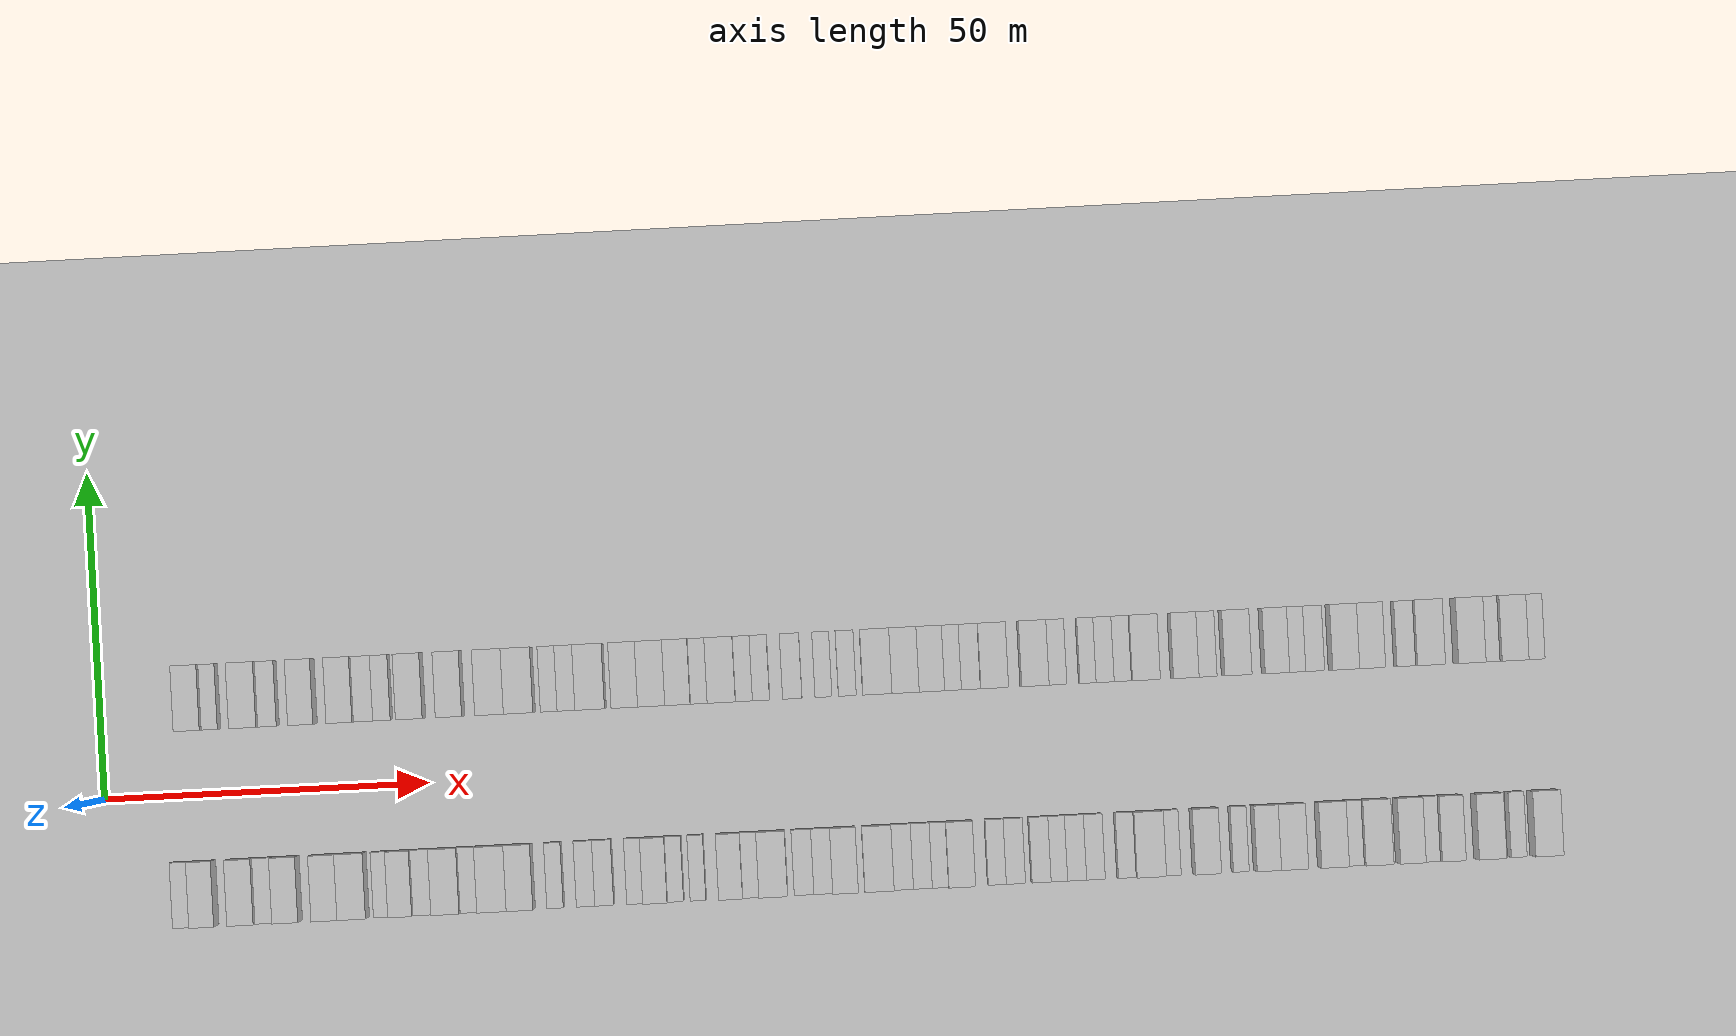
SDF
<?xml version="1.0" encoding="utf-8"?>

<sdf version="1.6">

   <world name="default">

      <gui fullscreen="0">

         <camera name="user_camera">

            <pose>-15 0 4.57585 0 0 0</pose>

            <view_controller>orbit</view_controller>

         </camera>

      </gui>

      <scene>

         <sky>

           <clouds>

             <speed>12</speed>

           </clouds>

         </sky>

         <ambient>0.4 0.4 0.4 1</ambient>

         <background>0.7 0.7 0.7 1</background>

         <shadows>1</shadows>

      </scene>

      <gravity>0 0 -9.8066</gravity>

      <magnetic_field>6e-06 2.3e-05 -4.2e-05</magnetic_field>

      <physics default="0" name="default_physics" type="ode">

         <ode>

            <solver>

               <type>quick</type>

               <iters>10</iters>

               <sor>1.0</sor>

               <use_dynamic_moi_rescaling>0</use_dynamic_moi_rescaling>

            </solver>

            <constraints>

               <cfm>0</cfm>

               <erp>0.2</erp>

               <contact_max_correcting_vel>100</contact_max_correcting_vel>

               <contact_surface_layer>0.001</contact_surface_layer>

            </constraints>

         </ode>

         <max_step_size>0.004</max_step_size>

         <real_time_factor>1</real_time_factor>

         <real_time_update_rate>250</real_time_update_rate>

      </physics>

      <light name="sun" type="directional">

         <cast_shadows>1</cast_shadows>

         <pose>0 0 10 0 0 0</pose>

         <diffuse>0.8 0.8 0.8 1</diffuse>

         <specular>0.2 0.2 0.2 1</specular>

         <attenuation>

            <range>1000</range>

            <constant>0.9</constant>

            <linear>0.01</linear>

            <quadratic>0.001</quadratic>

         </attenuation>

         <direction>-0.5 0.1 -0.9</direction>

      </light>

      <include>

         <name>ground_plane_1</name>

         <uri>model://HANNAS_ground_plane</uri>

         <pose>0 0 0  0 0 0</pose>

      </include>

      <include>

         <name>ground_plane_2</name>

         <uri>model://HANNAS_ground_plane</uri>

         <pose>100 0 0  0 0 0</pose>

      </include>

      <model name="building_1">

         <static>1</static>

         <pose frame="">13.9863 15.0000 0 0.000000 0.000000 1.570796</pose>

         <link name="link">

            <pose frame="">0 0 4.50 0 0 0</pose>

            <collision name="collision">

               <geometry>

                  <box>

                     <size>10.0000 3.9726 9.0000</size>

                  </box>

               </geometry>

               <max_contacts>10</max_contacts>

               <surface>

                  <contact>

                     <ode/>

                  </contact>

                  <bounce/>

                  <friction>

                     <torsional>

                        <ode/>

                     </torsional>

                     <ode/>

                  </friction>

               </surface>

            </collision>

            <visual name="visual">

               <cast_shadows>0</cast_shadows>

               <geometry>

                  <box>

                     <size>10.0000 3.9726 9.0000</size>

                  </box>

               </geometry>

               <material>

                  <script>

                     <uri>model://HANNAS_wall/materials/scripts</uri>

                     <uri>model://HANNAS_wall/materials/textures</uri>

                     <name>vrc/HANNAS_wall</name>

                  </script>

               </material>

            </visual>

            <self_collide>0</self_collide>

            <enable_wind>0</enable_wind>

            <kinematic>0</kinematic>

         </link>

      </model>

      <model name="building_2">

         <static>1</static>

         <pose frame="">17.2035 15.0000 0 0.000000 0.000000 1.570796</pose>

         <link name="link">

            <pose frame="">0 0 3.00 0 0 0</pose>

            <collision name="collision">

               <geometry>

                  <box>

                     <size>10.0000 2.4617 6.0000</size>

                  </box>

               </geometry>

               <max_contacts>10</max_contacts>

               <surface>

                  <contact>

                     <ode/>

                  </contact>

                  <bounce/>

                  <friction>

                     <torsional>

                        <ode/>

                     </torsional>

                     <ode/>

                  </friction>

               </surface>

            </collision>

            <visual name="visual">

               <cast_shadows>0</cast_shadows>

               <geometry>

                  <box>

                     <size>10.0000 2.4617 6.0000</size>

                  </box>

               </geometry>

               <material>

                  <script>

                     <uri>model://HANNAS_wall/materials/scripts</uri>

                     <uri>model://HANNAS_wall/materials/textures</uri>

                     <name>vrc/HANNAS_wall</name>

                  </script>

               </material>

            </visual>

            <self_collide>0</self_collide>

            <enable_wind>0</enable_wind>

            <kinematic>0</kinematic>

         </link>

      </model>

      <model name="building_3">

         <static>1</static>

         <pose frame="">22.5151 15.0000 0 0.000000 0.000000 1.570796</pose>

         <link name="link">

            <pose frame="">0 0 4.50 0 0 0</pose>

            <collision name="collision">

               <geometry>

                  <box>

                     <size>10.0000 4.1615 9.0000</size>

                  </box>

               </geometry>

               <max_contacts>10</max_contacts>

               <surface>

                  <contact>

                     <ode/>

                  </contact>

                  <bounce/>

                  <friction>

                     <torsional>

                        <ode/>

                     </torsional>

                     <ode/>

                  </friction>

               </surface>

            </collision>

            <visual name="visual">

               <cast_shadows>0</cast_shadows>

               <geometry>

                  <box>

                     <size>10.0000 4.1615 9.0000</size>

                  </box>

               </geometry>

               <material>

                  <script>

                     <uri>model://HANNAS_wall/materials/scripts</uri>

                     <uri>model://HANNAS_wall/materials/textures</uri>

                     <name>vrc/HANNAS_wall</name>

                  </script>

               </material>

            </visual>

            <self_collide>0</self_collide>

            <enable_wind>0</enable_wind>

            <kinematic>0</kinematic>

         </link>

      </model>

      <model name="building_4">

         <static>1</static>

         <pose frame="">26.0151 15.0000 0 0.000000 0.000000 1.570796</pose>

         <link name="link">

            <pose frame="">0 0 3.00 0 0 0</pose>

            <collision name="collision">

               <geometry>

                  <box>

                     <size>10.0000 2.8385 6.0000</size>

                  </box>

               </geometry>

               <max_contacts>10</max_contacts>

               <surface>

                  <contact>

                     <ode/>

                  </contact>

                  <bounce/>

                  <friction>

                     <torsional>

                        <ode/>

                     </torsional>

                     <ode/>

                  </friction>

               </surface>

            </collision>

            <visual name="visual">

               <cast_shadows>0</cast_shadows>

               <geometry>

                  <box>

                     <size>10.0000 2.8385 6.0000</size>

                  </box>

               </geometry>

               <material>

                  <script>

                     <uri>model://HANNAS_wall/materials/scripts</uri>

                     <uri>model://HANNAS_wall/materials/textures</uri>

                     <name>vrc/HANNAS_wall</name>

                  </script>

               </material>

            </visual>

            <self_collide>0</self_collide>

            <enable_wind>0</enable_wind>

            <kinematic>0</kinematic>

         </link>

      </model>

      <model name="building_5">

         <static>1</static>

         <pose frame="">31.3539 15.0000 0 0.000000 0.000000 1.570796</pose>

         <link name="link">

            <pose frame="">0 0 4.50 0 0 0</pose>

            <collision name="collision">

               <geometry>

                  <box>

                     <size>10.0000 3.8392 9.0000</size>

                  </box>

               </geometry>

               <max_contacts>10</max_contacts>

               <surface>

                  <contact>

                     <ode/>

                  </contact>

                  <bounce/>

                  <friction>

                     <torsional>

                        <ode/>

                     </torsional>

                     <ode/>

                  </friction>

               </surface>

            </collision>

            <visual name="visual">

               <cast_shadows>0</cast_shadows>

               <geometry>

                  <box>

                     <size>10.0000 3.8392 9.0000</size>

                  </box>

               </geometry>

               <material>

                  <script>

                     <uri>model://HANNAS_wall/materials/scripts</uri>

                     <uri>model://HANNAS_wall/materials/textures</uri>

                     <name>vrc/HANNAS_wall</name>

                  </script>

               </material>

            </visual>

            <self_collide>0</self_collide>

            <enable_wind>0</enable_wind>

            <kinematic>0</kinematic>

         </link>

      </model>

      <model name="building_6">

         <static>1</static>

         <pose frame="">37.2430 15.0000 0 0.000000 0.000000 1.570796</pose>

         <link name="link">

            <pose frame="">0 0 4.50 0 0 0</pose>

            <collision name="collision">

               <geometry>

                  <box>

                     <size>10.0000 3.9389 9.0000</size>

                  </box>

               </geometry>

               <max_contacts>10</max_contacts>

               <surface>

                  <contact>

                     <ode/>

                  </contact>

                  <bounce/>

                  <friction>

                     <torsional>

                        <ode/>

                     </torsional>

                     <ode/>

                  </friction>

               </surface>

            </collision>

            <visual name="visual">

               <cast_shadows>0</cast_shadows>

               <geometry>

                  <box>

                     <size>10.0000 3.9389 9.0000</size>

                  </box>

               </geometry>

               <material>

                  <script>

                     <uri>model://HANNAS_wall/materials/scripts</uri>

                     <uri>model://HANNAS_wall/materials/textures</uri>

                     <name>vrc/HANNAS_wall</name>

                  </script>

               </material>

            </visual>

            <self_collide>0</self_collide>

            <enable_wind>0</enable_wind>

            <kinematic>0</kinematic>

         </link>

      </model>

      <model name="building_7">

         <static>1</static>

         <pose frame="">40.6891 15.0000 0 0.000000 0.000000 1.570796</pose>

         <link name="link">

            <pose frame="">0 0 3.00 0 0 0</pose>

            <collision name="collision">

               <geometry>

                  <box>

                     <size>10.0000 2.9532 6.0000</size>

                  </box>

               </geometry>

               <max_contacts>10</max_contacts>

               <surface>

                  <contact>

                     <ode/>

                  </contact>

                  <bounce/>

                  <friction>

                     <torsional>

                        <ode/>

                     </torsional>

                     <ode/>

                  </friction>

               </surface>

            </collision>

            <visual name="visual">

               <cast_shadows>0</cast_shadows>

               <geometry>

                  <box>

                     <size>10.0000 2.9532 6.0000</size>

                  </box>

               </geometry>

               <material>

                  <script>

                     <uri>model://HANNAS_wall/materials/scripts</uri>

                     <uri>model://HANNAS_wall/materials/textures</uri>

                     <name>vrc/HANNAS_wall</name>

                  </script>

               </material>

            </visual>

            <self_collide>0</self_collide>

            <enable_wind>0</enable_wind>

            <kinematic>0</kinematic>

         </link>

      </model>

      <model name="building_8">

         <static>1</static>

         <pose frame="">43.5024 15.0000 0 0.000000 0.000000 1.570796</pose>

         <link name="link">

            <pose frame="">0 0 3.00 0 0 0</pose>

            <collision name="collision">

               <geometry>

                  <box>

                     <size>10.0000 2.6734 6.0000</size>

                  </box>

               </geometry>

               <max_contacts>10</max_contacts>

               <surface>

                  <contact>

                     <ode/>

                  </contact>

                  <bounce/>

                  <friction>

                     <torsional>

                        <ode/>

                     </torsional>

                     <ode/>

                  </friction>

               </surface>

            </collision>

            <visual name="visual">

               <cast_shadows>0</cast_shadows>

               <geometry>

                  <box>

                     <size>10.0000 2.6734 6.0000</size>

                  </box>

               </geometry>

               <material>

                  <script>

                     <uri>model://HANNAS_wall/materials/scripts</uri>

                     <uri>model://HANNAS_wall/materials/textures</uri>

                     <name>vrc/HANNAS_wall</name>

                  </script>

               </material>

            </visual>

            <self_collide>0</self_collide>

            <enable_wind>0</enable_wind>

            <kinematic>0</kinematic>

         </link>

      </model>

      <model name="building_9">

         <static>1</static>

         <pose frame="">47.8759 15.0000 0 0.000000 0.000000 1.570796</pose>

         <link name="link">

            <pose frame="">0 0 4.50 0 0 0</pose>

            <collision name="collision">

               <geometry>

                  <box>

                     <size>10.0000 4.0736 9.0000</size>

                  </box>

               </geometry>

               <max_contacts>10</max_contacts>

               <surface>

                  <contact>

                     <ode/>

                  </contact>

                  <bounce/>

                  <friction>

                     <torsional>

                        <ode/>

                     </torsional>

                     <ode/>

                  </friction>

               </surface>

            </collision>

            <visual name="visual">

               <cast_shadows>0</cast_shadows>

               <geometry>

                  <box>

                     <size>10.0000 4.0736 9.0000</size>

                  </box>

               </geometry>

               <material>

                  <script>

                     <uri>model://HANNAS_wall/materials/scripts</uri>

                     <uri>model://HANNAS_wall/materials/textures</uri>

                     <name>vrc/HANNAS_wall</name>

                  </script>

               </material>

            </visual>

            <self_collide>0</self_collide>

            <enable_wind>0</enable_wind>

            <kinematic>0</kinematic>

         </link>

      </model>

      <model name="building_10">

         <static>1</static>

         <pose frame="">53.9139 15.0000 0 0.000000 0.000000 1.570796</pose>

         <link name="link">

            <pose frame="">0 0 4.50 0 0 0</pose>

            <collision name="collision">

               <geometry>

                  <box>

                     <size>10.0000 4.0025 9.0000</size>

                  </box>

               </geometry>

               <max_contacts>10</max_contacts>

               <surface>

                  <contact>

                     <ode/>

                  </contact>

                  <bounce/>

                  <friction>

                     <torsional>

                        <ode/>

                     </torsional>

                     <ode/>

                  </friction>

               </surface>

            </collision>

            <visual name="visual">

               <cast_shadows>0</cast_shadows>

               <geometry>

                  <box>

                     <size>10.0000 4.0025 9.0000</size>

                  </box>

               </geometry>

               <material>

                  <script>

                     <uri>model://HANNAS_wall/materials/scripts</uri>

                     <uri>model://HANNAS_wall/materials/textures</uri>

                     <name>vrc/HANNAS_wall</name>

                  </script>

               </material>

            </visual>

            <self_collide>0</self_collide>

            <enable_wind>0</enable_wind>

            <kinematic>0</kinematic>

         </link>

      </model>

      <model name="building_11">

         <static>1</static>

         <pose frame="">60.0964 15.0000 0 0.000000 0.000000 1.570796</pose>

         <link name="link">

            <pose frame="">0 0 4.50 0 0 0</pose>

            <collision name="collision">

               <geometry>

                  <box>

                     <size>10.0000 4.3625 9.0000</size>

                  </box>

               </geometry>

               <max_contacts>10</max_contacts>

               <surface>

                  <contact>

                     <ode/>

                  </contact>

                  <bounce/>

                  <friction>

                     <torsional>

                        <ode/>

                     </torsional>

                     <ode/>

                  </friction>

               </surface>

            </collision>

            <visual name="visual">

               <cast_shadows>0</cast_shadows>

               <geometry>

                  <box>

                     <size>10.0000 4.3625 9.0000</size>

                  </box>

               </geometry>

               <material>

                  <script>

                     <uri>model://HANNAS_wall/materials/scripts</uri>

                     <uri>model://HANNAS_wall/materials/textures</uri>

                     <name>vrc/HANNAS_wall</name>

                  </script>

               </material>

            </visual>

            <self_collide>0</self_collide>

            <enable_wind>0</enable_wind>

            <kinematic>0</kinematic>

         </link>

      </model>

      <model name="building_12">

         <static>1</static>

         <pose frame="">64.5238 15.0000 0 0.000000 0.000000 1.570796</pose>

         <link name="link">

            <pose frame="">0 0 4.50 0 0 0</pose>

            <collision name="collision">

               <geometry>

                  <box>

                     <size>10.0000 4.4922 9.0000</size>

                  </box>

               </geometry>

               <max_contacts>10</max_contacts>

               <surface>

                  <contact>

                     <ode/>

                  </contact>

                  <bounce/>

                  <friction>

                     <torsional>

                        <ode/>

                     </torsional>

                     <ode/>

                  </friction>

               </surface>

            </collision>

            <visual name="visual">

               <cast_shadows>0</cast_shadows>

               <geometry>

                  <box>

                     <size>10.0000 4.4922 9.0000</size>

                  </box>

               </geometry>

               <material>

                  <script>

                     <uri>model://HANNAS_wall/materials/scripts</uri>

                     <uri>model://HANNAS_wall/materials/textures</uri>

                     <name>vrc/HANNAS_wall</name>

                  </script>

               </material>

            </visual>

            <self_collide>0</self_collide>

            <enable_wind>0</enable_wind>

            <kinematic>0</kinematic>

         </link>

      </model>

      <model name="building_13">

         <static>1</static>

         <pose frame="">69.0498 15.0000 0 0.000000 0.000000 1.570796</pose>

         <link name="link">

            <pose frame="">0 0 3.00 0 0 0</pose>

            <collision name="collision">

               <geometry>

                  <box>

                     <size>10.0000 2.5598 6.0000</size>

                  </box>

               </geometry>

               <max_contacts>10</max_contacts>

               <surface>

                  <contact>

                     <ode/>

                  </contact>

                  <bounce/>

                  <friction>

                     <torsional>

                        <ode/>

                     </torsional>

                     <ode/>

                  </friction>

               </surface>

            </collision>

            <visual name="visual">

               <cast_shadows>0</cast_shadows>

               <geometry>

                  <box>

                     <size>10.0000 2.5598 6.0000</size>

                  </box>

               </geometry>

               <material>

                  <script>

                     <uri>model://HANNAS_wall/materials/scripts</uri>

                     <uri>model://HANNAS_wall/materials/textures</uri>

                     <name>vrc/HANNAS_wall</name>

                  </script>

               </material>

            </visual>

            <self_collide>0</self_collide>

            <enable_wind>0</enable_wind>

            <kinematic>0</kinematic>

         </link>

      </model>

      <model name="building_14">

         <static>1</static>

         <pose frame="">71.7501 15.0000 0 0.000000 0.000000 1.570796</pose>

         <link name="link">

            <pose frame="">0 0 3.00 0 0 0</pose>

            <collision name="collision">

               <geometry>

                  <box>

                     <size>10.0000 2.8408 6.0000</size>

                  </box>

               </geometry>

               <max_contacts>10</max_contacts>

               <surface>

                  <contact>

                     <ode/>

                  </contact>

                  <bounce/>

                  <friction>

                     <torsional>

                        <ode/>

                     </torsional>

                     <ode/>

                  </friction>

               </surface>

            </collision>

            <visual name="visual">

               <cast_shadows>0</cast_shadows>

               <geometry>

                  <box>

                     <size>10.0000 2.8408 6.0000</size>

                  </box>

               </geometry>

               <material>

                  <script>

                     <uri>model://HANNAS_wall/materials/scripts</uri>

                     <uri>model://HANNAS_wall/materials/textures</uri>

                     <name>vrc/HANNAS_wall</name>

                  </script>

               </material>

            </visual>

            <self_collide>0</self_collide>

            <enable_wind>0</enable_wind>

            <kinematic>0</kinematic>

         </link>

      </model>

      <model name="building_15">

         <static>1</static>

         <pose frame="">75.4201 15.0000 0 0.000000 0.000000 1.570796</pose>

         <link name="link">

            <pose frame="">0 0 4.50 0 0 0</pose>

            <collision name="collision">

               <geometry>

                  <box>

                     <size>10.0000 4.4993 9.0000</size>

                  </box>

               </geometry>

               <max_contacts>10</max_contacts>

               <surface>

                  <contact>

                     <ode/>

                  </contact>

                  <bounce/>

                  <friction>

                     <torsional>

                        <ode/>

                     </torsional>

                     <ode/>

                  </friction>

               </surface>

            </collision>

            <visual name="visual">

               <cast_shadows>0</cast_shadows>

               <geometry>

                  <box>

                     <size>10.0000 4.4993 9.0000</size>

                  </box>

               </geometry>

               <material>

                  <script>

                     <uri>model://HANNAS_wall/materials/scripts</uri>

                     <uri>model://HANNAS_wall/materials/textures</uri>

                     <name>vrc/HANNAS_wall</name>

                  </script>

               </material>

            </visual>

            <self_collide>0</self_collide>

            <enable_wind>0</enable_wind>

            <kinematic>0</kinematic>

         </link>

      </model>

      <model name="building_16">

         <static>1</static>

         <pose frame="">80.6914 15.0000 0 0.000000 0.000000 1.570796</pose>

         <link name="link">

            <pose frame="">0 0 4.50 0 0 0</pose>

            <collision name="collision">

               <geometry>

                  <box>

                     <size>10.0000 4.0434 9.0000</size>

                  </box>

               </geometry>

               <max_contacts>10</max_contacts>

               <surface>

                  <contact>

                     <ode/>

                  </contact>

                  <bounce/>

                  <friction>

                     <torsional>

                        <ode/>

                     </torsional>

                     <ode/>

                  </friction>

               </surface>

            </collision>

            <visual name="visual">

               <cast_shadows>0</cast_shadows>

               <geometry>

                  <box>

                     <size>10.0000 4.0434 9.0000</size>

                  </box>

               </geometry>

               <material>

                  <script>

                     <uri>model://HANNAS_wall/materials/scripts</uri>

                     <uri>model://HANNAS_wall/materials/textures</uri>

                     <name>vrc/HANNAS_wall</name>

                  </script>

               </material>

            </visual>

            <self_collide>0</self_collide>

            <enable_wind>0</enable_wind>

            <kinematic>0</kinematic>

         </link>

      </model>

      <model name="building_17">

         <static>1</static>

         <pose frame="">84.7833 15.0000 0 0.000000 0.000000 1.570796</pose>

         <link name="link">

            <pose frame="">0 0 4.50 0 0 0</pose>

            <collision name="collision">

               <geometry>

                  <box>

                     <size>10.0000 4.1405 9.0000</size>

                  </box>

               </geometry>

               <max_contacts>10</max_contacts>

               <surface>

                  <contact>

                     <ode/>

                  </contact>

                  <bounce/>

                  <friction>

                     <torsional>

                        <ode/>

                     </torsional>

                     <ode/>

                  </friction>

               </surface>

            </collision>

            <visual name="visual">

               <cast_shadows>0</cast_shadows>

               <geometry>

                  <box>

                     <size>10.0000 4.1405 9.0000</size>

                  </box>

               </geometry>

               <material>

                  <script>

                     <uri>model://HANNAS_wall/materials/scripts</uri>

                     <uri>model://HANNAS_wall/materials/textures</uri>

                     <name>vrc/HANNAS_wall</name>

                  </script>

               </material>

            </visual>

            <self_collide>0</self_collide>

            <enable_wind>0</enable_wind>

            <kinematic>0</kinematic>

         </link>

      </model>

      <model name="building_18">

         <static>1</static>

         <pose frame="">88.7812 15.0000 0 0.000000 0.000000 1.570796</pose>

         <link name="link">

            <pose frame="">0 0 4.50 0 0 0</pose>

            <collision name="collision">

               <geometry>

                  <box>

                     <size>10.0000 3.8553 9.0000</size>

                  </box>

               </geometry>

               <max_contacts>10</max_contacts>

               <surface>

                  <contact>

                     <ode/>

                  </contact>

                  <bounce/>

                  <friction>

                     <torsional>

                        <ode/>

                     </torsional>

                     <ode/>

                  </friction>

               </surface>

            </collision>

            <visual name="visual">

               <cast_shadows>0</cast_shadows>

               <geometry>

                  <box>

                     <size>10.0000 3.8553 9.0000</size>

                  </box>

               </geometry>

               <material>

                  <script>

                     <uri>model://HANNAS_wall/materials/scripts</uri>

                     <uri>model://HANNAS_wall/materials/textures</uri>

                     <name>vrc/HANNAS_wall</name>

                  </script>

               </material>

            </visual>

            <self_collide>0</self_collide>

            <enable_wind>0</enable_wind>

            <kinematic>0</kinematic>

         </link>

      </model>

      <model name="building_19">

         <static>1</static>

         <pose frame="">92.0073 15.0000 0 0.000000 0.000000 1.570796</pose>

         <link name="link">

            <pose frame="">0 0 3.00 0 0 0</pose>

            <collision name="collision">

               <geometry>

                  <box>

                     <size>10.0000 2.5967 6.0000</size>

                  </box>

               </geometry>

               <max_contacts>10</max_contacts>

               <surface>

                  <contact>

                     <ode/>

                  </contact>

                  <bounce/>

                  <friction>

                     <torsional>

                        <ode/>

                     </torsional>

                     <ode/>

                  </friction>

               </surface>

            </collision>

            <visual name="visual">

               <cast_shadows>0</cast_shadows>

               <geometry>

                  <box>

                     <size>10.0000 2.5967 6.0000</size>

                  </box>

               </geometry>

               <material>

                  <script>

                     <uri>model://HANNAS_wall/materials/scripts</uri>

                     <uri>model://HANNAS_wall/materials/textures</uri>

                     <name>vrc/HANNAS_wall</name>

                  </script>

               </material>

            </visual>

            <self_collide>0</self_collide>

            <enable_wind>0</enable_wind>

            <kinematic>0</kinematic>

         </link>

      </model>

      <model name="building_20">

         <static>1</static>

         <pose frame="">95.4486 15.0000 0 0.000000 0.000000 1.570796</pose>

         <link name="link">

            <pose frame="">0 0 4.50 0 0 0</pose>

            <collision name="collision">

               <geometry>

                  <box>

                     <size>10.0000 4.2859 9.0000</size>

                  </box>

               </geometry>

               <max_contacts>10</max_contacts>

               <surface>

                  <contact>

                     <ode/>

                  </contact>

                  <bounce/>

                  <friction>

                     <torsional>

                        <ode/>

                     </torsional>

                     <ode/>

                  </friction>

               </surface>

            </collision>

            <visual name="visual">

               <cast_shadows>0</cast_shadows>

               <geometry>

                  <box>

                     <size>10.0000 4.2859 9.0000</size>

                  </box>

               </geometry>

               <material>

                  <script>

                     <uri>model://HANNAS_wall/materials/scripts</uri>

                     <uri>model://HANNAS_wall/materials/textures</uri>

                     <name>vrc/HANNAS_wall</name>

                  </script>

               </material>

            </visual>

            <self_collide>0</self_collide>

            <enable_wind>0</enable_wind>

            <kinematic>0</kinematic>

         </link>

      </model>

      <model name="building_21">

         <static>1</static>

         <pose frame="">98.8770 15.0000 0 0.000000 0.000000 1.570796</pose>

         <link name="link">

            <pose frame="">0 0 3.00 0 0 0</pose>

            <collision name="collision">

               <geometry>

                  <box>

                     <size>10.0000 2.5709 6.0000</size>

                  </box>

               </geometry>

               <max_contacts>10</max_contacts>

               <surface>

                  <contact>

                     <ode/>

                  </contact>

                  <bounce/>

                  <friction>

                     <torsional>

                        <ode/>

                     </torsional>

                     <ode/>

                  </friction>

               </surface>

            </collision>

            <visual name="visual">

               <cast_shadows>0</cast_shadows>

               <geometry>

                  <box>

                     <size>10.0000 2.5709 6.0000</size>

                  </box>

               </geometry>

               <material>

                  <script>

                     <uri>model://HANNAS_wall/materials/scripts</uri>

                     <uri>model://HANNAS_wall/materials/textures</uri>

                     <name>vrc/HANNAS_wall</name>

                  </script>

               </material>

            </visual>

            <self_collide>0</self_collide>

            <enable_wind>0</enable_wind>

            <kinematic>0</kinematic>

         </link>

      </model>

      <model name="building_22">

         <static>1</static>

         <pose frame="">101.4697 15.0000 0 0.000000 0.000000 1.570796</pose>

         <link name="link">

            <pose frame="">0 0 3.00 0 0 0</pose>

            <collision name="collision">

               <geometry>

                  <box>

                     <size>10.0000 2.6144 6.0000</size>

                  </box>

               </geometry>

               <max_contacts>10</max_contacts>

               <surface>

                  <contact>

                     <ode/>

                  </contact>

                  <bounce/>

                  <friction>

                     <torsional>

                        <ode/>

                     </torsional>

                     <ode/>

                  </friction>

               </surface>

            </collision>

            <visual name="visual">

               <cast_shadows>0</cast_shadows>

               <geometry>

                  <box>

                     <size>10.0000 2.6144 6.0000</size>

                  </box>

               </geometry>

               <material>

                  <script>

                     <uri>model://HANNAS_wall/materials/scripts</uri>

                     <uri>model://HANNAS_wall/materials/textures</uri>

                     <name>vrc/HANNAS_wall</name>

                  </script>

               </material>

            </visual>

            <self_collide>0</self_collide>

            <enable_wind>0</enable_wind>

            <kinematic>0</kinematic>

         </link>

      </model>

      <model name="building_23">

         <static>1</static>

         <pose frame="">106.2533 15.0000 0 0.000000 0.000000 1.570796</pose>

         <link name="link">

            <pose frame="">0 0 3.00 0 0 0</pose>

            <collision name="collision">

               <geometry>

                  <box>

                     <size>10.0000 2.9528 6.0000</size>

                  </box>

               </geometry>

               <max_contacts>10</max_contacts>

               <surface>

                  <contact>

                     <ode/>

                  </contact>

                  <bounce/>

                  <friction>

                     <torsional>

                        <ode/>

                     </torsional>

                     <ode/>

                  </friction>

               </surface>

            </collision>

            <visual name="visual">

               <cast_shadows>0</cast_shadows>

               <geometry>

                  <box>

                     <size>10.0000 2.9528 6.0000</size>

                  </box>

               </geometry>

               <material>

                  <script>

                     <uri>model://HANNAS_wall/materials/scripts</uri>

                     <uri>model://HANNAS_wall/materials/textures</uri>

                     <name>vrc/HANNAS_wall</name>

                  </script>

               </material>

            </visual>

            <self_collide>0</self_collide>

            <enable_wind>0</enable_wind>

            <kinematic>0</kinematic>

         </link>

      </model>

      <model name="building_24">

         <static>1</static>

         <pose frame="">111.0208 15.0000 0 0.000000 0.000000 1.570796</pose>

         <link name="link">

            <pose frame="">0 0 3.00 0 0 0</pose>

            <collision name="collision">

               <geometry>

                  <box>

                     <size>10.0000 2.5822 6.0000</size>

                  </box>

               </geometry>

               <max_contacts>10</max_contacts>

               <surface>

                  <contact>

                     <ode/>

                  </contact>

                  <bounce/>

                  <friction>

                     <torsional>

                        <ode/>

                     </torsional>

                     <ode/>

                  </friction>

               </surface>

            </collision>

            <visual name="visual">

               <cast_shadows>0</cast_shadows>

               <geometry>

                  <box>

                     <size>10.0000 2.5822 6.0000</size>

                  </box>

               </geometry>

               <material>

                  <script>

                     <uri>model://HANNAS_wall/materials/scripts</uri>

                     <uri>model://HANNAS_wall/materials/textures</uri>

                     <name>vrc/HANNAS_wall</name>

                  </script>

               </material>

            </visual>

            <self_collide>0</self_collide>

            <enable_wind>0</enable_wind>

            <kinematic>0</kinematic>

         </link>

      </model>

      <model name="building_25">

         <static>1</static>

         <pose frame="">114.6714 15.0000 0 0.000000 0.000000 1.570796</pose>

         <link name="link">

            <pose frame="">0 0 3.00 0 0 0</pose>

            <collision name="collision">

               <geometry>

                  <box>

                     <size>10.0000 2.7189 6.0000</size>

                  </box>

               </geometry>

               <max_contacts>10</max_contacts>

               <surface>

                  <contact>

                     <ode/>

                  </contact>

                  <bounce/>

                  <friction>

                     <torsional>

                        <ode/>

                     </torsional>

                     <ode/>

                  </friction>

               </surface>

            </collision>

            <visual name="visual">

               <cast_shadows>0</cast_shadows>

               <geometry>

                  <box>

                     <size>10.0000 2.7189 6.0000</size>

                  </box>

               </geometry>

               <material>

                  <script>

                     <uri>model://HANNAS_wall/materials/scripts</uri>

                     <uri>model://HANNAS_wall/materials/textures</uri>

                     <name>vrc/HANNAS_wall</name>

                  </script>

               </material>

            </visual>

            <self_collide>0</self_collide>

            <enable_wind>0</enable_wind>

            <kinematic>0</kinematic>

         </link>

      </model>

      <model name="building_26">

         <static>1</static>

         <pose frame="">119.2425 15.0000 0 0.000000 0.000000 1.570796</pose>

         <link name="link">

            <pose frame="">0 0 4.50 0 0 0</pose>

            <collision name="collision">

               <geometry>

                  <box>

                     <size>10.0000 4.4233 9.0000</size>

                  </box>

               </geometry>

               <max_contacts>10</max_contacts>

               <surface>

                  <contact>

                     <ode/>

                  </contact>

                  <bounce/>

                  <friction>

                     <torsional>

                        <ode/>

                     </torsional>

                     <ode/>

                  </friction>

               </surface>

            </collision>

            <visual name="visual">

               <cast_shadows>0</cast_shadows>

               <geometry>

                  <box>

                     <size>10.0000 4.4233 9.0000</size>

                  </box>

               </geometry>

               <material>

                  <script>

                     <uri>model://HANNAS_wall/materials/scripts</uri>

                     <uri>model://HANNAS_wall/materials/textures</uri>

                     <name>vrc/HANNAS_wall</name>

                  </script>

               </material>

            </visual>

            <self_collide>0</self_collide>

            <enable_wind>0</enable_wind>

            <kinematic>0</kinematic>

         </link>

      </model>

      <model name="building_27">

         <static>1</static>

         <pose frame="">123.5292 15.0000 0 0.000000 0.000000 1.570796</pose>

         <link name="link">

            <pose frame="">0 0 4.50 0 0 0</pose>

            <collision name="collision">

               <geometry>

                  <box>

                     <size>10.0000 4.1503 9.0000</size>

                  </box>

               </geometry>

               <max_contacts>10</max_contacts>

               <surface>

                  <contact>

                     <ode/>

                  </contact>

                  <bounce/>

                  <friction>

                     <torsional>

                        <ode/>

                     </torsional>

                     <ode/>

                  </friction>

               </surface>

            </collision>

            <visual name="visual">

               <cast_shadows>0</cast_shadows>

               <geometry>

                  <box>

                     <size>10.0000 4.1503 9.0000</size>

                  </box>

               </geometry>

               <material>

                  <script>

                     <uri>model://HANNAS_wall/materials/scripts</uri>

                     <uri>model://HANNAS_wall/materials/textures</uri>

                     <name>vrc/HANNAS_wall</name>

                  </script>

               </material>

            </visual>

            <self_collide>0</self_collide>

            <enable_wind>0</enable_wind>

            <kinematic>0</kinematic>

         </link>

      </model>

      <model name="building_28">

         <static>1</static>

         <pose frame="">127.5365 15.0000 0 0.000000 0.000000 1.570796</pose>

         <link name="link">

            <pose frame="">0 0 4.50 0 0 0</pose>

            <collision name="collision">

               <geometry>

                  <box>

                     <size>10.0000 3.8643 9.0000</size>

                  </box>

               </geometry>

               <max_contacts>10</max_contacts>

               <surface>

                  <contact>

                     <ode/>

                  </contact>

                  <bounce/>

                  <friction>

                     <torsional>

                        <ode/>

                     </torsional>

                     <ode/>

                  </friction>

               </surface>

            </collision>

            <visual name="visual">

               <cast_shadows>0</cast_shadows>

               <geometry>

                  <box>

                     <size>10.0000 3.8643 9.0000</size>

                  </box>

               </geometry>

               <material>

                  <script>

                     <uri>model://HANNAS_wall/materials/scripts</uri>

                     <uri>model://HANNAS_wall/materials/textures</uri>

                     <name>vrc/HANNAS_wall</name>

                  </script>

               </material>

            </visual>

            <self_collide>0</self_collide>

            <enable_wind>0</enable_wind>

            <kinematic>0</kinematic>

         </link>

      </model>

      <model name="building_29">

         <static>1</static>

         <pose frame="">130.7800 15.0000 0 0.000000 0.000000 1.570796</pose>

         <link name="link">

            <pose frame="">0 0 3.00 0 0 0</pose>

            <collision name="collision">

               <geometry>

                  <box>

                     <size>10.0000 2.6229 6.0000</size>

                  </box>

               </geometry>

               <max_contacts>10</max_contacts>

               <surface>

                  <contact>

                     <ode/>

                  </contact>

                  <bounce/>

                  <friction>

                     <torsional>

                        <ode/>

                     </torsional>

                     <ode/>

                  </friction>

               </surface>

            </collision>

            <visual name="visual">

               <cast_shadows>0</cast_shadows>

               <geometry>

                  <box>

                     <size>10.0000 2.6229 6.0000</size>

                  </box>

               </geometry>

               <material>

                  <script>

                     <uri>model://HANNAS_wall/materials/scripts</uri>

                     <uri>model://HANNAS_wall/materials/textures</uri>

                     <name>vrc/HANNAS_wall</name>

                  </script>

               </material>

            </visual>

            <self_collide>0</self_collide>

            <enable_wind>0</enable_wind>

            <kinematic>0</kinematic>

         </link>

      </model>

      <model name="building_30">

         <static>1</static>

         <pose frame="">133.5405 15.0000 0 0.000000 0.000000 1.570796</pose>

         <link name="link">

            <pose frame="">0 0 3.00 0 0 0</pose>

            <collision name="collision">

               <geometry>

                  <box>

                     <size>10.0000 2.8981 6.0000</size>

                  </box>

               </geometry>

               <max_contacts>10</max_contacts>

               <surface>

                  <contact>

                     <ode/>

                  </contact>

                  <bounce/>

                  <friction>

                     <torsional>

                        <ode/>

                     </torsional>

                     <ode/>

                  </friction>

               </surface>

            </collision>

            <visual name="visual">

               <cast_shadows>0</cast_shadows>

               <geometry>

                  <box>

                     <size>10.0000 2.8981 6.0000</size>

                  </box>

               </geometry>

               <material>

                  <script>

                     <uri>model://HANNAS_wall/materials/scripts</uri>

                     <uri>model://HANNAS_wall/materials/textures</uri>

                     <name>vrc/HANNAS_wall</name>

                  </script>

               </material>

            </visual>

            <self_collide>0</self_collide>

            <enable_wind>0</enable_wind>

            <kinematic>0</kinematic>

         </link>

      </model>

      <model name="building_31">

         <static>1</static>

         <pose frame="">137.0973 15.0000 0 0.000000 0.000000 1.570796</pose>

         <link name="link">

            <pose frame="">0 0 4.50 0 0 0</pose>

            <collision name="collision">

               <geometry>

                  <box>

                     <size>10.0000 4.2155 9.0000</size>

                  </box>

               </geometry>

               <max_contacts>10</max_contacts>

               <surface>

                  <contact>

                     <ode/>

                  </contact>

                  <bounce/>

                  <friction>

                     <torsional>

                        <ode/>

                     </torsional>

                     <ode/>

                  </friction>

               </surface>

            </collision>

            <visual name="visual">

               <cast_shadows>0</cast_shadows>

               <geometry>

                  <box>

                     <size>10.0000 4.2155 9.0000</size>

                  </box>

               </geometry>

               <material>

                  <script>

                     <uri>model://HANNAS_wall/materials/scripts</uri>

                     <uri>model://HANNAS_wall/materials/textures</uri>

                     <name>vrc/HANNAS_wall</name>

                  </script>

               </material>

            </visual>

            <self_collide>0</self_collide>

            <enable_wind>0</enable_wind>

            <kinematic>0</kinematic>

         </link>

      </model>

      <model name="building_32">

         <static>1</static>

         <pose frame="">143.2945 15.0000 0 0.000000 0.000000 1.570796</pose>

         <link name="link">

            <pose frame="">0 0 4.50 0 0 0</pose>

            <collision name="collision">

               <geometry>

                  <box>

                     <size>10.0000 4.1790 9.0000</size>

                  </box>

               </geometry>

               <max_contacts>10</max_contacts>

               <surface>

                  <contact>

                     <ode/>

                  </contact>

                  <bounce/>

                  <friction>

                     <torsional>

                        <ode/>

                     </torsional>

                     <ode/>

                  </friction>

               </surface>

            </collision>

            <visual name="visual">

               <cast_shadows>0</cast_shadows>

               <geometry>

                  <box>

                     <size>10.0000 4.1790 9.0000</size>

                  </box>

               </geometry>

               <material>

                  <script>

                     <uri>model://HANNAS_wall/materials/scripts</uri>

                     <uri>model://HANNAS_wall/materials/textures</uri>

                     <name>vrc/HANNAS_wall</name>

                  </script>

               </material>

            </visual>

            <self_collide>0</self_collide>

            <enable_wind>0</enable_wind>

            <kinematic>0</kinematic>

         </link>

      </model>

      <model name="building_33">

         <static>1</static>

         <pose frame="">146.7900 15.0000 0 0.000000 0.000000 1.570796</pose>

         <link name="link">

            <pose frame="">0 0 3.00 0 0 0</pose>

            <collision name="collision">

               <geometry>

                  <box>

                     <size>10.0000 2.8119 6.0000</size>

                  </box>

               </geometry>

               <max_contacts>10</max_contacts>

               <surface>

                  <contact>

                     <ode/>

                  </contact>

                  <bounce/>

                  <friction>

                     <torsional>

                        <ode/>

                     </torsional>

                     <ode/>

                  </friction>

               </surface>

            </collision>

            <visual name="visual">

               <cast_shadows>0</cast_shadows>

               <geometry>

                  <box>

                     <size>10.0000 2.8119 6.0000</size>

                  </box>

               </geometry>

               <material>

                  <script>

                     <uri>model://HANNAS_wall/materials/scripts</uri>

                     <uri>model://HANNAS_wall/materials/textures</uri>

                     <name>vrc/HANNAS_wall</name>

                  </script>

               </material>

            </visual>

            <self_collide>0</self_collide>

            <enable_wind>0</enable_wind>

            <kinematic>0</kinematic>

         </link>

      </model>

      <model name="building_34">

         <static>1</static>

         <pose frame="">151.4294 15.0000 0 0.000000 0.000000 1.570796</pose>

         <link name="link">

            <pose frame="">0 0 3.00 0 0 0</pose>

            <collision name="collision">

               <geometry>

                  <box>

                     <size>10.0000 2.4668 6.0000</size>

                  </box>

               </geometry>

               <max_contacts>10</max_contacts>

               <surface>

                  <contact>

                     <ode/>

                  </contact>

                  <bounce/>

                  <friction>

                     <torsional>

                        <ode/>

                     </torsional>

                     <ode/>

                  </friction>

               </surface>

            </collision>

            <visual name="visual">

               <cast_shadows>0</cast_shadows>

               <geometry>

                  <box>

                     <size>10.0000 2.4668 6.0000</size>

                  </box>

               </geometry>

               <material>

                  <script>

                     <uri>model://HANNAS_wall/materials/scripts</uri>

                     <uri>model://HANNAS_wall/materials/textures</uri>

                     <name>vrc/HANNAS_wall</name>

                  </script>

               </material>

            </visual>

            <self_collide>0</self_collide>

            <enable_wind>0</enable_wind>

            <kinematic>0</kinematic>

         </link>

      </model>

      <model name="building_35">

         <static>1</static>

         <pose frame="">154.0448 15.0000 0 0.000000 0.000000 1.570796</pose>

         <link name="link">

            <pose frame="">0 0 3.00 0 0 0</pose>

            <collision name="collision">

               <geometry>

                  <box>

                     <size>10.0000 2.7641 6.0000</size>

                  </box>

               </geometry>

               <max_contacts>10</max_contacts>

               <surface>

                  <contact>

                     <ode/>

                  </contact>

                  <bounce/>

                  <friction>

                     <torsional>

                        <ode/>

                     </torsional>

                     <ode/>

                  </friction>

               </surface>

            </collision>

            <visual name="visual">

               <cast_shadows>0</cast_shadows>

               <geometry>

                  <box>

                     <size>10.0000 2.7641 6.0000</size>

                  </box>

               </geometry>

               <material>

                  <script>

                     <uri>model://HANNAS_wall/materials/scripts</uri>

                     <uri>model://HANNAS_wall/materials/textures</uri>

                     <name>vrc/HANNAS_wall</name>

                  </script>

               </material>

            </visual>

            <self_collide>0</self_collide>

            <enable_wind>0</enable_wind>

            <kinematic>0</kinematic>

         </link>

      </model>

      <model name="building_36">

         <static>1</static>

         <pose frame="">156.7458 15.0000 0 0.000000 0.000000 1.570796</pose>

         <link name="link">

            <pose frame="">0 0 3.00 0 0 0</pose>

            <collision name="collision">

               <geometry>

                  <box>

                     <size>10.0000 2.6380 6.0000</size>

                  </box>

               </geometry>

               <max_contacts>10</max_contacts>

               <surface>

                  <contact>

                     <ode/>

                  </contact>

                  <bounce/>

                  <friction>

                     <torsional>

                        <ode/>

                     </torsional>

                     <ode/>

                  </friction>

               </surface>

            </collision>

            <visual name="visual">

               <cast_shadows>0</cast_shadows>

               <geometry>

                  <box>

                     <size>10.0000 2.6380 6.0000</size>

                  </box>

               </geometry>

               <material>

                  <script>

                     <uri>model://HANNAS_wall/materials/scripts</uri>

                     <uri>model://HANNAS_wall/materials/textures</uri>

                     <name>vrc/HANNAS_wall</name>

                  </script>

               </material>

            </visual>

            <self_collide>0</self_collide>

            <enable_wind>0</enable_wind>

            <kinematic>0</kinematic>

         </link>

      </model>

      <model name="building_37">

         <static>1</static>

         <pose frame="">160.1915 15.0000 0 0.000000 0.000000 1.570796</pose>

         <link name="link">

            <pose frame="">0 0 4.50 0 0 0</pose>

            <collision name="collision">

               <geometry>

                  <box>

                     <size>10.0000 4.2535 9.0000</size>

                  </box>

               </geometry>

               <max_contacts>10</max_contacts>

               <surface>

                  <contact>

                     <ode/>

                  </contact>

                  <bounce/>

                  <friction>

                     <torsional>

                        <ode/>

                     </torsional>

                     <ode/>

                  </friction>

               </surface>

            </collision>

            <visual name="visual">

               <cast_shadows>0</cast_shadows>

               <geometry>

                  <box>

                     <size>10.0000 4.2535 9.0000</size>

                  </box>

               </geometry>

               <material>

                  <script>

                     <uri>model://HANNAS_wall/materials/scripts</uri>

                     <uri>model://HANNAS_wall/materials/textures</uri>

                     <name>vrc/HANNAS_wall</name>

                  </script>

               </material>

            </visual>

            <self_collide>0</self_collide>

            <enable_wind>0</enable_wind>

            <kinematic>0</kinematic>

         </link>

      </model>

      <model name="building_38">

         <static>1</static>

         <pose frame="">166.2654 15.0000 0 0.000000 0.000000 1.570796</pose>

         <link name="link">

            <pose frame="">0 0 4.50 0 0 0</pose>

            <collision name="collision">

               <geometry>

                  <box>

                     <size>10.0000 3.8942 9.0000</size>

                  </box>

               </geometry>

               <max_contacts>10</max_contacts>

               <surface>

                  <contact>

                     <ode/>

                  </contact>

                  <bounce/>

                  <friction>

                     <torsional>

                        <ode/>

                     </torsional>

                     <ode/>

                  </friction>

               </surface>

            </collision>

            <visual name="visual">

               <cast_shadows>0</cast_shadows>

               <geometry>

                  <box>

                     <size>10.0000 3.8942 9.0000</size>

                  </box>

               </geometry>

               <material>

                  <script>

                     <uri>model://HANNAS_wall/materials/scripts</uri>

                     <uri>model://HANNAS_wall/materials/textures</uri>

                     <name>vrc/HANNAS_wall</name>

                  </script>

               </material>

            </visual>

            <self_collide>0</self_collide>

            <enable_wind>0</enable_wind>

            <kinematic>0</kinematic>

         </link>

      </model>

      <model name="building_39">

         <static>1</static>

         <pose frame="">169.6782 15.0000 0 0.000000 0.000000 1.570796</pose>

         <link name="link">

            <pose frame="">0 0 3.00 0 0 0</pose>

            <collision name="collision">

               <geometry>

                  <box>

                     <size>10.0000 2.9316 6.0000</size>

                  </box>

               </geometry>

               <max_contacts>10</max_contacts>

               <surface>

                  <contact>

                     <ode/>

                  </contact>

                  <bounce/>

                  <friction>

                     <torsional>

                        <ode/>

                     </torsional>

                     <ode/>

                  </friction>

               </surface>

            </collision>

            <visual name="visual">

               <cast_shadows>0</cast_shadows>

               <geometry>

                  <box>

                     <size>10.0000 2.9316 6.0000</size>

                  </box>

               </geometry>

               <material>

                  <script>

                     <uri>model://HANNAS_wall/materials/scripts</uri>

                     <uri>model://HANNAS_wall/materials/textures</uri>

                     <name>vrc/HANNAS_wall</name>

                  </script>

               </material>

            </visual>

            <self_collide>0</self_collide>

            <enable_wind>0</enable_wind>

            <kinematic>0</kinematic>

         </link>

      </model>

      <model name="building_40">

         <static>1</static>

         <pose frame="">174.2125 15.0000 0 0.000000 0.000000 1.570796</pose>

         <link name="link">

            <pose frame="">0 0 4.50 0 0 0</pose>

            <collision name="collision">

               <geometry>

                  <box>

                     <size>10.0000 4.1370 9.0000</size>

                  </box>

               </geometry>

               <max_contacts>10</max_contacts>

               <surface>

                  <contact>

                     <ode/>

                  </contact>

                  <bounce/>

                  <friction>

                     <torsional>

                        <ode/>

                     </torsional>

                     <ode/>

                  </friction>

               </surface>

            </collision>

            <visual name="visual">

               <cast_shadows>0</cast_shadows>

               <geometry>

                  <box>

                     <size>10.0000 4.1370 9.0000</size>

                  </box>

               </geometry>

               <material>

                  <script>

                     <uri>model://HANNAS_wall/materials/scripts</uri>

                     <uri>model://HANNAS_wall/materials/textures</uri>

                     <name>vrc/HANNAS_wall</name>

                  </script>

               </material>

            </visual>

            <self_collide>0</self_collide>

            <enable_wind>0</enable_wind>

            <kinematic>0</kinematic>

         </link>

      </model>

      <model name="building_41">

         <static>1</static>

         <pose frame="">180.1501 15.0000 0 0.000000 0.000000 1.570796</pose>

         <link name="link">

            <pose frame="">0 0 4.50 0 0 0</pose>

            <collision name="collision">

               <geometry>

                  <box>

                     <size>10.0000 3.7381 9.0000</size>

                  </box>

               </geometry>

               <max_contacts>10</max_contacts>

               <surface>

                  <contact>

                     <ode/>

                  </contact>

                  <bounce/>

                  <friction>

                     <torsional>

                        <ode/>

                     </torsional>

                     <ode/>

                  </friction>

               </surface>

            </collision>

            <visual name="visual">

               <cast_shadows>0</cast_shadows>

               <geometry>

                  <box>

                     <size>10.0000 3.7381 9.0000</size>

                  </box>

               </geometry>

               <material>

                  <script>

                     <uri>model://HANNAS_wall/materials/scripts</uri>

                     <uri>model://HANNAS_wall/materials/textures</uri>

                     <name>vrc/HANNAS_wall</name>

                  </script>

               </material>

            </visual>

            <self_collide>0</self_collide>

            <enable_wind>0</enable_wind>

            <kinematic>0</kinematic>

         </link>

      </model>

      <model name="building_42">

         <static>1</static>

         <pose frame="">183.3578 15.0000 0 0.000000 0.000000 1.570796</pose>

         <link name="link">

            <pose frame="">0 0 3.00 0 0 0</pose>

            <collision name="collision">

               <geometry>

                  <box>

                     <size>10.0000 2.6774 6.0000</size>

                  </box>

               </geometry>

               <max_contacts>10</max_contacts>

               <surface>

                  <contact>

                     <ode/>

                  </contact>

                  <bounce/>

                  <friction>

                     <torsional>

                        <ode/>

                     </torsional>

                     <ode/>

                  </friction>

               </surface>

            </collision>

            <visual name="visual">

               <cast_shadows>0</cast_shadows>

               <geometry>

                  <box>

                     <size>10.0000 2.6774 6.0000</size>

                  </box>

               </geometry>

               <material>

                  <script>

                     <uri>model://HANNAS_wall/materials/scripts</uri>

                     <uri>model://HANNAS_wall/materials/textures</uri>

                     <name>vrc/HANNAS_wall</name>

                  </script>

               </material>

            </visual>

            <self_collide>0</self_collide>

            <enable_wind>0</enable_wind>

            <kinematic>0</kinematic>

         </link>

      </model>

      <model name="building_43">

         <static>1</static>

         <pose frame="">186.1347 15.0000 0 0.000000 0.000000 1.570796</pose>

         <link name="link">

            <pose frame="">0 0 3.00 0 0 0</pose>

            <collision name="collision">

               <geometry>

                  <box>

                     <size>10.0000 2.8764 6.0000</size>

                  </box>

               </geometry>

               <max_contacts>10</max_contacts>

               <surface>

                  <contact>

                     <ode/>

                  </contact>

                  <bounce/>

                  <friction>

                     <torsional>

                        <ode/>

                     </torsional>

                     <ode/>

                  </friction>

               </surface>

            </collision>

            <visual name="visual">

               <cast_shadows>0</cast_shadows>

               <geometry>

                  <box>

                     <size>10.0000 2.8764 6.0000</size>

                  </box>

               </geometry>

               <material>

                  <script>

                     <uri>model://HANNAS_wall/materials/scripts</uri>

                     <uri>model://HANNAS_wall/materials/textures</uri>

                     <name>vrc/HANNAS_wall</name>

                  </script>

               </material>

            </visual>

            <self_collide>0</self_collide>

            <enable_wind>0</enable_wind>

            <kinematic>0</kinematic>

         </link>

      </model>

      <model name="building_44">

         <static>1</static>

         <pose frame="">190.6257 15.0000 0 0.000000 0.000000 1.570796</pose>

         <link name="link">

            <pose frame="">0 0 4.50 0 0 0</pose>

            <collision name="collision">

               <geometry>

                  <box>

                     <size>10.0000 4.1056 9.0000</size>

                  </box>

               </geometry>

               <max_contacts>10</max_contacts>

               <surface>

                  <contact>

                     <ode/>

                  </contact>

                  <bounce/>

                  <friction>

                     <torsional>

                        <ode/>

                     </torsional>

                     <ode/>

                  </friction>

               </surface>

            </collision>

            <visual name="visual">

               <cast_shadows>0</cast_shadows>

               <geometry>

                  <box>

                     <size>10.0000 4.1056 9.0000</size>

                  </box>

               </geometry>

               <material>

                  <script>

                     <uri>model://HANNAS_wall/materials/scripts</uri>

                     <uri>model://HANNAS_wall/materials/textures</uri>

                     <name>vrc/HANNAS_wall</name>

                  </script>

               </material>

            </visual>

            <self_collide>0</self_collide>

            <enable_wind>0</enable_wind>

            <kinematic>0</kinematic>

         </link>

      </model>

      <model name="building_45">

         <static>1</static>

         <pose frame="">194.6477 15.0000 0 0.000000 0.000000 1.570796</pose>

         <link name="link">

            <pose frame="">0 0 4.50 0 0 0</pose>

            <collision name="collision">

               <geometry>

                  <box>

                     <size>10.0000 3.9384 9.0000</size>

                  </box>

               </geometry>

               <max_contacts>10</max_contacts>

               <surface>

                  <contact>

                     <ode/>

                  </contact>

                  <bounce/>

                  <friction>

                     <torsional>

                        <ode/>

                     </torsional>

                     <ode/>

                  </friction>

               </surface>

            </collision>

            <visual name="visual">

               <cast_shadows>0</cast_shadows>

               <geometry>

                  <box>

                     <size>10.0000 3.9384 9.0000</size>

                  </box>

               </geometry>

               <material>

                  <script>

                     <uri>model://HANNAS_wall/materials/scripts</uri>

                     <uri>model://HANNAS_wall/materials/textures</uri>

                     <name>vrc/HANNAS_wall</name>

                  </script>

               </material>

            </visual>

            <self_collide>0</self_collide>

            <enable_wind>0</enable_wind>

            <kinematic>0</kinematic>

         </link>

      </model>

      <model name="building_46">

         <static>1</static>

         <pose frame="">200.0471 15.0000 0 0.000000 0.000000 1.570796</pose>

         <link name="link">

            <pose frame="">0 0 3.00 0 0 0</pose>

            <collision name="collision">

               <geometry>

                  <box>

                     <size>10.0000 2.8604 6.0000</size>

                  </box>

               </geometry>

               <max_contacts>10</max_contacts>

               <surface>

                  <contact>

                     <ode/>

                  </contact>

                  <bounce/>

                  <friction>

                     <torsional>

                        <ode/>

                     </torsional>

                     <ode/>

                  </friction>

               </surface>

            </collision>

            <visual name="visual">

               <cast_shadows>0</cast_shadows>

               <geometry>

                  <box>

                     <size>10.0000 2.8604 6.0000</size>

                  </box>

               </geometry>

               <material>

                  <script>

                     <uri>model://HANNAS_wall/materials/scripts</uri>

                     <uri>model://HANNAS_wall/materials/textures</uri>

                     <name>vrc/HANNAS_wall</name>

                  </script>

               </material>

            </visual>

            <self_collide>0</self_collide>

            <enable_wind>0</enable_wind>

            <kinematic>0</kinematic>

         </link>

      </model>

      <model name="building_47">

         <static>1</static>

         <pose frame="">203.6051 15.0000 0 0.000000 0.000000 1.570796</pose>

         <link name="link">

            <pose frame="">0 0 4.50 0 0 0</pose>

            <collision name="collision">

               <geometry>

                  <box>

                     <size>10.0000 4.2556 9.0000</size>

                  </box>

               </geometry>

               <max_contacts>10</max_contacts>

               <surface>

                  <contact>

                     <ode/>

                  </contact>

                  <bounce/>

                  <friction>

                     <torsional>

                        <ode/>

                     </torsional>

                     <ode/>

                  </friction>

               </surface>

            </collision>

            <visual name="visual">

               <cast_shadows>0</cast_shadows>

               <geometry>

                  <box>

                     <size>10.0000 4.2556 9.0000</size>

                  </box>

               </geometry>

               <material>

                  <script>

                     <uri>model://HANNAS_wall/materials/scripts</uri>

                     <uri>model://HANNAS_wall/materials/textures</uri>

                     <name>vrc/HANNAS_wall</name>

                  </script>

               </material>

            </visual>

            <self_collide>0</self_collide>

            <enable_wind>0</enable_wind>

            <kinematic>0</kinematic>

         </link>

      </model>

      <model name="building_48">

         <static>1</static>

         <pose frame="">209.8230 15.0000 0 0.000000 0.000000 1.570796</pose>

         <link name="link">

            <pose frame="">0 0 4.50 0 0 0</pose>

            <collision name="collision">

               <geometry>

                  <box>

                     <size>10.0000 4.1801 9.0000</size>

                  </box>

               </geometry>

               <max_contacts>10</max_contacts>

               <surface>

                  <contact>

                     <ode/>

                  </contact>

                  <bounce/>

                  <friction>

                     <torsional>

                        <ode/>

                     </torsional>

                     <ode/>

                  </friction>

               </surface>

            </collision>

            <visual name="visual">

               <cast_shadows>0</cast_shadows>

               <geometry>

                  <box>

                     <size>10.0000 4.1801 9.0000</size>

                  </box>

               </geometry>

               <material>

                  <script>

                     <uri>model://HANNAS_wall/materials/scripts</uri>

                     <uri>model://HANNAS_wall/materials/textures</uri>

                     <name>vrc/HANNAS_wall</name>

                  </script>

               </material>

            </visual>

            <self_collide>0</self_collide>

            <enable_wind>0</enable_wind>

            <kinematic>0</kinematic>

         </link>

      </model>

      <model name="building_49">

         <static>1</static>

         <pose frame="">213.1358 15.0000 0 0.000000 0.000000 1.570796</pose>

         <link name="link">

            <pose frame="">0 0 3.00 0 0 0</pose>

            <collision name="collision">

               <geometry>

                  <box>

                     <size>10.0000 2.4456 6.0000</size>

                  </box>

               </geometry>

               <max_contacts>10</max_contacts>

               <surface>

                  <contact>

                     <ode/>

                  </contact>

                  <bounce/>

                  <friction>

                     <torsional>

                        <ode/>

                     </torsional>

                     <ode/>

                  </friction>

               </surface>

            </collision>

            <visual name="visual">

               <cast_shadows>0</cast_shadows>

               <geometry>

                  <box>

                     <size>10.0000 2.4456 6.0000</size>

                  </box>

               </geometry>

               <material>

                  <script>

                     <uri>model://HANNAS_wall/materials/scripts</uri>

                     <uri>model://HANNAS_wall/materials/textures</uri>

                     <name>vrc/HANNAS_wall</name>

                  </script>

               </material>

            </visual>

            <self_collide>0</self_collide>

            <enable_wind>0</enable_wind>

            <kinematic>0</kinematic>

         </link>

      </model>

      <model name="building_50">

         <static>1</static>

         <pose frame="">216.4056 15.0000 0 0.000000 0.000000 1.570796</pose>

         <link name="link">

            <pose frame="">0 0 4.50 0 0 0</pose>

            <collision name="collision">

               <geometry>

                  <box>

                     <size>10.0000 4.0941 9.0000</size>

                  </box>

               </geometry>

               <max_contacts>10</max_contacts>

               <surface>

                  <contact>

                     <ode/>

                  </contact>

                  <bounce/>

                  <friction>

                     <torsional>

                        <ode/>

                     </torsional>

                     <ode/>

                  </friction>

               </surface>

            </collision>

            <visual name="visual">

               <cast_shadows>0</cast_shadows>

               <geometry>

                  <box>

                     <size>10.0000 4.0941 9.0000</size>

                  </box>

               </geometry>

               <material>

                  <script>

                     <uri>model://HANNAS_wall/materials/scripts</uri>

                     <uri>model://HANNAS_wall/materials/textures</uri>

                     <name>vrc/HANNAS_wall</name>

                  </script>

               </material>

            </visual>

            <self_collide>0</self_collide>

            <enable_wind>0</enable_wind>

            <kinematic>0</kinematic>

         </link>

      </model>

      <model name="building_51">

         <static>1</static>

         <pose frame="">219.8437 15.0000 0 0.000000 0.000000 1.570796</pose>

         <link name="link">

            <pose frame="">0 0 3.00 0 0 0</pose>

            <collision name="collision">

               <geometry>

                  <box>

                     <size>10.0000 2.7820 6.0000</size>

                  </box>

               </geometry>

               <max_contacts>10</max_contacts>

               <surface>

                  <contact>

                     <ode/>

                  </contact>

                  <bounce/>

                  <friction>

                     <torsional>

                        <ode/>

                     </torsional>

                     <ode/>

                  </friction>

               </surface>

            </collision>

            <visual name="visual">

               <cast_shadows>0</cast_shadows>

               <geometry>

                  <box>

                     <size>10.0000 2.7820 6.0000</size>

                  </box>

               </geometry>

               <material>

                  <script>

                     <uri>model://HANNAS_wall/materials/scripts</uri>

                     <uri>model://HANNAS_wall/materials/textures</uri>

                     <name>vrc/HANNAS_wall</name>

                  </script>

               </material>

            </visual>

            <self_collide>0</self_collide>

            <enable_wind>0</enable_wind>

            <kinematic>0</kinematic>

         </link>

      </model>

      <model name="building_52">

         <static>1</static>

         <pose frame="">11.3973 -15.0000 0 0.000000 0.000000 1.570796</pose>

         <link name="link">

            <pose frame="">0 0 3.00 0 0 0</pose>

            <collision name="collision">

               <geometry>

                  <box>

                     <size>10.0000 2.7946 6.0000</size>

                  </box>

               </geometry>

               <max_contacts>10</max_contacts>

               <surface>

                  <contact>

                     <ode/>

                  </contact>

                  <bounce/>

                  <friction>

                     <torsional>

                        <ode/>

                     </torsional>

                     <ode/>

                  </friction>

               </surface>

            </collision>

            <visual name="visual">

               <cast_shadows>0</cast_shadows>

               <geometry>

                  <box>

                     <size>10.0000 2.7946 6.0000</size>

                  </box>

               </geometry>

               <material>

                  <script>

                     <uri>model://HANNAS_wall/materials/scripts</uri>

                     <uri>model://HANNAS_wall/materials/textures</uri>

                     <name>vrc/HANNAS_wall</name>

                  </script>

               </material>

            </visual>

            <self_collide>0</self_collide>

            <enable_wind>0</enable_wind>

            <kinematic>0</kinematic>

         </link>

      </model>

      <model name="building_53">

         <static>1</static>

         <pose frame="">14.6870 -15.0000 0 0.000000 0.000000 1.570796</pose>

         <link name="link">

            <pose frame="">0 0 4.50 0 0 0</pose>

            <collision name="collision">

               <geometry>

                  <box>

                     <size>10.0000 3.7847 9.0000</size>

                  </box>

               </geometry>

               <max_contacts>10</max_contacts>

               <surface>

                  <contact>

                     <ode/>

                  </contact>

                  <bounce/>

                  <friction>

                     <torsional>

                        <ode/>

                     </torsional>

                     <ode/>

                  </friction>

               </surface>

            </collision>

            <visual name="visual">

               <cast_shadows>0</cast_shadows>

               <geometry>

                  <box>

                     <size>10.0000 3.7847 9.0000</size>

                  </box>

               </geometry>

               <material>

                  <script>

                     <uri>model://HANNAS_wall/materials/scripts</uri>

                     <uri>model://HANNAS_wall/materials/textures</uri>

                     <name>vrc/HANNAS_wall</name>

                  </script>

               </material>

            </visual>

            <self_collide>0</self_collide>

            <enable_wind>0</enable_wind>

            <kinematic>0</kinematic>

         </link>

      </model>

      <model name="building_54">

         <static>1</static>

         <pose frame="">20.5842 -15.0000 0 0.000000 0.000000 1.570796</pose>

         <link name="link">

            <pose frame="">0 0 4.50 0 0 0</pose>

            <collision name="collision">

               <geometry>

                  <box>

                     <size>10.0000 4.0096 9.0000</size>

                  </box>

               </geometry>

               <max_contacts>10</max_contacts>

               <surface>

                  <contact>

                     <ode/>

                  </contact>

                  <bounce/>

                  <friction>

                     <torsional>

                        <ode/>

                     </torsional>

                     <ode/>

                  </friction>

               </surface>

            </collision>

            <visual name="visual">

               <cast_shadows>0</cast_shadows>

               <geometry>

                  <box>

                     <size>10.0000 4.0096 9.0000</size>

                  </box>

               </geometry>

               <material>

                  <script>

                     <uri>model://HANNAS_wall/materials/scripts</uri>

                     <uri>model://HANNAS_wall/materials/textures</uri>

                     <name>vrc/HANNAS_wall</name>

                  </script>

               </material>

            </visual>

            <self_collide>0</self_collide>

            <enable_wind>0</enable_wind>

            <kinematic>0</kinematic>

         </link>

      </model>

      <model name="building_55">

         <static>1</static>

         <pose frame="">24.0114 -15.0000 0 0.000000 0.000000 1.570796</pose>

         <link name="link">

            <pose frame="">0 0 3.00 0 0 0</pose>

            <collision name="collision">

               <geometry>

                  <box>

                     <size>10.0000 2.8448 6.0000</size>

                  </box>

               </geometry>

               <max_contacts>10</max_contacts>

               <surface>

                  <contact>

                     <ode/>

                  </contact>

                  <bounce/>

                  <friction>

                     <torsional>

                        <ode/>

                     </torsional>

                     <ode/>

                  </friction>

               </surface>

            </collision>

            <visual name="visual">

               <cast_shadows>0</cast_shadows>

               <geometry>

                  <box>

                     <size>10.0000 2.8448 6.0000</size>

                  </box>

               </geometry>

               <material>

                  <script>

                     <uri>model://HANNAS_wall/materials/scripts</uri>

                     <uri>model://HANNAS_wall/materials/textures</uri>

                     <name>vrc/HANNAS_wall</name>

                  </script>

               </material>

            </visual>

            <self_collide>0</self_collide>

            <enable_wind>0</enable_wind>

            <kinematic>0</kinematic>

         </link>

      </model>

      <model name="building_56">

         <static>1</static>

         <pose frame="">27.4137 -15.0000 0 0.000000 0.000000 1.570796</pose>

         <link name="link">

            <pose frame="">0 0 4.50 0 0 0</pose>

            <collision name="collision">

               <geometry>

                  <box>

                     <size>10.0000 3.9599 9.0000</size>

                  </box>

               </geometry>

               <max_contacts>10</max_contacts>

               <surface>

                  <contact>

                     <ode/>

                  </contact>

                  <bounce/>

                  <friction>

                     <torsional>

                        <ode/>

                     </torsional>

                     <ode/>

                  </friction>

               </surface>

            </collision>

            <visual name="visual">

               <cast_shadows>0</cast_shadows>

               <geometry>

                  <box>

                     <size>10.0000 3.9599 9.0000</size>

                  </box>

               </geometry>

               <material>

                  <script>

                     <uri>model://HANNAS_wall/materials/scripts</uri>

                     <uri>model://HANNAS_wall/materials/textures</uri>

                     <name>vrc/HANNAS_wall</name>

                  </script>

               </material>

            </visual>

            <self_collide>0</self_collide>

            <enable_wind>0</enable_wind>

            <kinematic>0</kinematic>

         </link>

      </model>

      <model name="building_57">

         <static>1</static>

         <pose frame="">33.3716 -15.0000 0 0.000000 0.000000 1.570796</pose>

         <link name="link">

            <pose frame="">0 0 4.50 0 0 0</pose>

            <collision name="collision">

               <geometry>

                  <box>

                     <size>10.0000 3.9559 9.0000</size>

                  </box>

               </geometry>

               <max_contacts>10</max_contacts>

               <surface>

                  <contact>

                     <ode/>

                  </contact>

                  <bounce/>

                  <friction>

                     <torsional>

                        <ode/>

                     </torsional>

                     <ode/>

                  </friction>

               </surface>

            </collision>

            <visual name="visual">

               <cast_shadows>0</cast_shadows>

               <geometry>

                  <box>

                     <size>10.0000 3.9559 9.0000</size>

                  </box>

               </geometry>

               <material>

                  <script>

                     <uri>model://HANNAS_wall/materials/scripts</uri>

                     <uri>model://HANNAS_wall/materials/textures</uri>

                     <name>vrc/HANNAS_wall</name>

                  </script>

               </material>

            </visual>

            <self_collide>0</self_collide>

            <enable_wind>0</enable_wind>

            <kinematic>0</kinematic>

         </link>

      </model>

      <model name="building_58">

         <static>1</static>

         <pose frame="">37.5189 -15.0000 0 0.000000 0.000000 1.570796</pose>

         <link name="link">

            <pose frame="">0 0 4.50 0 0 0</pose>

            <collision name="collision">

               <geometry>

                  <box>

                     <size>10.0000 4.3388 9.0000</size>

                  </box>

               </geometry>

               <max_contacts>10</max_contacts>

               <surface>

                  <contact>

                     <ode/>

                  </contact>

                  <bounce/>

                  <friction>

                     <torsional>

                        <ode/>

                     </torsional>

                     <ode/>

                  </friction>

               </surface>

            </collision>

            <visual name="visual">

               <cast_shadows>0</cast_shadows>

               <geometry>

                  <box>

                     <size>10.0000 4.3388 9.0000</size>

                  </box>

               </geometry>

               <material>

                  <script>

                     <uri>model://HANNAS_wall/materials/scripts</uri>

                     <uri>model://HANNAS_wall/materials/textures</uri>

                     <name>vrc/HANNAS_wall</name>

                  </script>

               </material>

            </visual>

            <self_collide>0</self_collide>

            <enable_wind>0</enable_wind>

            <kinematic>0</kinematic>

         </link>

      </model>

      <model name="building_59">

         <static>1</static>

         <pose frame="">41.8885 -15.0000 0 0.000000 0.000000 1.570796</pose>

         <link name="link">

            <pose frame="">0 0 3.00 0 0 0</pose>

            <collision name="collision">

               <geometry>

                  <box>

                     <size>10.0000 2.4004 6.0000</size>

                  </box>

               </geometry>

               <max_contacts>10</max_contacts>

               <surface>

                  <contact>

                     <ode/>

                  </contact>

                  <bounce/>

                  <friction>

                     <torsional>

                        <ode/>

                     </torsional>

                     <ode/>

                  </friction>

               </surface>

            </collision>

            <visual name="visual">

               <cast_shadows>0</cast_shadows>

               <geometry>

                  <box>

                     <size>10.0000 2.4004 6.0000</size>

                  </box>

               </geometry>

               <material>

                  <script>

                     <uri>model://HANNAS_wall/materials/scripts</uri>

                     <uri>model://HANNAS_wall/materials/textures</uri>

                     <name>vrc/HANNAS_wall</name>

                  </script>

               </material>

            </visual>

            <self_collide>0</self_collide>

            <enable_wind>0</enable_wind>

            <kinematic>0</kinematic>

         </link>

      </model>

      <model name="building_60">

         <static>1</static>

         <pose frame="">44.9065 -15.0000 0 0.000000 0.000000 1.570796</pose>

         <link name="link">

            <pose frame="">0 0 4.50 0 0 0</pose>

            <collision name="collision">

               <geometry>

                  <box>

                     <size>10.0000 3.6356 9.0000</size>

                  </box>

               </geometry>

               <max_contacts>10</max_contacts>

               <surface>

                  <contact>

                     <ode/>

                  </contact>

                  <bounce/>

                  <friction>

                     <torsional>

                        <ode/>

                     </torsional>

                     <ode/>

                  </friction>

               </surface>

            </collision>

            <visual name="visual">

               <cast_shadows>0</cast_shadows>

               <geometry>

                  <box>

                     <size>10.0000 3.6356 9.0000</size>

                  </box>

               </geometry>

               <material>

                  <script>

                     <uri>model://HANNAS_wall/materials/scripts</uri>

                     <uri>model://HANNAS_wall/materials/textures</uri>

                     <name>vrc/HANNAS_wall</name>

                  </script>

               </material>

            </visual>

            <self_collide>0</self_collide>

            <enable_wind>0</enable_wind>

            <kinematic>0</kinematic>

         </link>

      </model>

      <model name="building_61">

         <static>1</static>

         <pose frame="">48.1842 -15.0000 0 0.000000 0.000000 1.570796</pose>

         <link name="link">

            <pose frame="">0 0 3.00 0 0 0</pose>

            <collision name="collision">

               <geometry>

                  <box>

                     <size>10.0000 2.9200 6.0000</size>

                  </box>

               </geometry>

               <max_contacts>10</max_contacts>

               <surface>

                  <contact>

                     <ode/>

                  </contact>

                  <bounce/>

                  <friction>

                     <torsional>

                        <ode/>

                     </torsional>

                     <ode/>

                  </friction>

               </surface>

            </collision>

            <visual name="visual">

               <cast_shadows>0</cast_shadows>

               <geometry>

                  <box>

                     <size>10.0000 2.9200 6.0000</size>

                  </box>

               </geometry>

               <material>

                  <script>

                     <uri>model://HANNAS_wall/materials/scripts</uri>

                     <uri>model://HANNAS_wall/materials/textures</uri>

                     <name>vrc/HANNAS_wall</name>

                  </script>

               </material>

            </visual>

            <self_collide>0</self_collide>

            <enable_wind>0</enable_wind>

            <kinematic>0</kinematic>

         </link>

      </model>

      <model name="building_62">

         <static>1</static>

         <pose frame="">51.7884 -15.0000 0 0.000000 0.000000 1.570796</pose>

         <link name="link">

            <pose frame="">0 0 4.50 0 0 0</pose>

            <collision name="collision">

               <geometry>

                  <box>

                     <size>10.0000 4.2884 9.0000</size>

                  </box>

               </geometry>

               <max_contacts>10</max_contacts>

               <surface>

                  <contact>

                     <ode/>

                  </contact>

                  <bounce/>

                  <friction>

                     <torsional>

                        <ode/>

                     </torsional>

                     <ode/>

                  </friction>

               </surface>

            </collision>

            <visual name="visual">

               <cast_shadows>0</cast_shadows>

               <geometry>

                  <box>

                     <size>10.0000 4.2884 9.0000</size>

                  </box>

               </geometry>

               <material>

                  <script>

                     <uri>model://HANNAS_wall/materials/scripts</uri>

                     <uri>model://HANNAS_wall/materials/textures</uri>

                     <name>vrc/HANNAS_wall</name>

                  </script>

               </material>

            </visual>

            <self_collide>0</self_collide>

            <enable_wind>0</enable_wind>

            <kinematic>0</kinematic>

         </link>

      </model>

      <model name="building_63">

         <static>1</static>

         <pose frame="">55.2880 -15.0000 0 0.000000 0.000000 1.570796</pose>

         <link name="link">

            <pose frame="">0 0 3.00 0 0 0</pose>

            <collision name="collision">

               <geometry>

                  <box>

                     <size>10.0000 2.7107 6.0000</size>

                  </box>

               </geometry>

               <max_contacts>10</max_contacts>

               <surface>

                  <contact>

                     <ode/>

                  </contact>

                  <bounce/>

                  <friction>

                     <torsional>

                        <ode/>

                     </torsional>

                     <ode/>

                  </friction>

               </surface>

            </collision>

            <visual name="visual">

               <cast_shadows>0</cast_shadows>

               <geometry>

                  <box>

                     <size>10.0000 2.7107 6.0000</size>

                  </box>

               </geometry>

               <material>

                  <script>

                     <uri>model://HANNAS_wall/materials/scripts</uri>

                     <uri>model://HANNAS_wall/materials/textures</uri>

                     <name>vrc/HANNAS_wall</name>

                  </script>

               </material>

            </visual>

            <self_collide>0</self_collide>

            <enable_wind>0</enable_wind>

            <kinematic>0</kinematic>

         </link>

      </model>

      <model name="building_64">

         <static>1</static>

         <pose frame="">58.8782 -15.0000 0 0.000000 0.000000 1.570796</pose>

         <link name="link">

            <pose frame="">0 0 4.50 0 0 0</pose>

            <collision name="collision">

               <geometry>

                  <box>

                     <size>10.0000 4.4697 9.0000</size>

                  </box>

               </geometry>

               <max_contacts>10</max_contacts>

               <surface>

                  <contact>

                     <ode/>

                  </contact>

                  <bounce/>

                  <friction>

                     <torsional>

                        <ode/>

                     </torsional>

                     <ode/>

                  </friction>

               </surface>

            </collision>

            <visual name="visual">

               <cast_shadows>0</cast_shadows>

               <geometry>

                  <box>

                     <size>10.0000 4.4697 9.0000</size>

                  </box>

               </geometry>

               <material>

                  <script>

                     <uri>model://HANNAS_wall/materials/scripts</uri>

                     <uri>model://HANNAS_wall/materials/textures</uri>

                     <name>vrc/HANNAS_wall</name>

                  </script>

               </material>

            </visual>

            <self_collide>0</self_collide>

            <enable_wind>0</enable_wind>

            <kinematic>0</kinematic>

         </link>

      </model>

      <model name="building_65">

         <static>1</static>

         <pose frame="">63.1442 -15.0000 0 0.000000 0.000000 1.570796</pose>

         <link name="link">

            <pose frame="">0 0 4.50 0 0 0</pose>

            <collision name="collision">

               <geometry>

                  <box>

                     <size>10.0000 4.0622 9.0000</size>

                  </box>

               </geometry>

               <max_contacts>10</max_contacts>

               <surface>

                  <contact>

                     <ode/>

                  </contact>

                  <bounce/>

                  <friction>

                     <torsional>

                        <ode/>

                     </torsional>

                     <ode/>

                  </friction>

               </surface>

            </collision>

            <visual name="visual">

               <cast_shadows>0</cast_shadows>

               <geometry>

                  <box>

                     <size>10.0000 4.0622 9.0000</size>

                  </box>

               </geometry>

               <material>

                  <script>

                     <uri>model://HANNAS_wall/materials/scripts</uri>

                     <uri>model://HANNAS_wall/materials/textures</uri>

                     <name>vrc/HANNAS_wall</name>

                  </script>

               </material>

            </visual>

            <self_collide>0</self_collide>

            <enable_wind>0</enable_wind>

            <kinematic>0</kinematic>

         </link>

      </model>

      <model name="building_66">

         <static>1</static>

         <pose frame="">68.4313 -15.0000 0 0.000000 0.000000 1.570796</pose>

         <link name="link">

            <pose frame="">0 0 3.00 0 0 0</pose>

            <collision name="collision">

               <geometry>

                  <box>

                     <size>10.0000 2.5121 6.0000</size>

                  </box>

               </geometry>

               <max_contacts>10</max_contacts>

               <surface>

                  <contact>

                     <ode/>

                  </contact>

                  <bounce/>

                  <friction>

                     <torsional>

                        <ode/>

                     </torsional>

                     <ode/>

                  </friction>

               </surface>

            </collision>

            <visual name="visual">

               <cast_shadows>0</cast_shadows>

               <geometry>

                  <box>

                     <size>10.0000 2.5121 6.0000</size>

                  </box>

               </geometry>

               <material>

                  <script>

                     <uri>model://HANNAS_wall/materials/scripts</uri>

                     <uri>model://HANNAS_wall/materials/textures</uri>

                     <name>vrc/HANNAS_wall</name>

                  </script>

               </material>

            </visual>

            <self_collide>0</self_collide>

            <enable_wind>0</enable_wind>

            <kinematic>0</kinematic>

         </link>

      </model>

      <model name="building_67">

         <static>1</static>

         <pose frame="">73.0961 -15.0000 0 0.000000 0.000000 1.570796</pose>

         <link name="link">

            <pose frame="">0 0 3.00 0 0 0</pose>

            <collision name="collision">

               <geometry>

                  <box>

                     <size>10.0000 2.8175 6.0000</size>

                  </box>

               </geometry>

               <max_contacts>10</max_contacts>

               <surface>

                  <contact>

                     <ode/>

                  </contact>

                  <bounce/>

                  <friction>

                     <torsional>

                        <ode/>

                     </torsional>

                     <ode/>

                  </friction>

               </surface>

            </collision>

            <visual name="visual">

               <cast_shadows>0</cast_shadows>

               <geometry>

                  <box>

                     <size>10.0000 2.8175 6.0000</size>

                  </box>

               </geometry>

               <material>

                  <script>

                     <uri>model://HANNAS_wall/materials/scripts</uri>

                     <uri>model://HANNAS_wall/materials/textures</uri>

                     <name>vrc/HANNAS_wall</name>

                  </script>

               </material>

            </visual>

            <self_collide>0</self_collide>

            <enable_wind>0</enable_wind>

            <kinematic>0</kinematic>

         </link>

      </model>

      <model name="building_68">

         <static>1</static>

         <pose frame="">75.9450 -15.0000 0 0.000000 0.000000 1.570796</pose>

         <link name="link">

            <pose frame="">0 0 3.00 0 0 0</pose>

            <collision name="collision">

               <geometry>

                  <box>

                     <size>10.0000 2.8802 6.0000</size>

                  </box>

               </geometry>

               <max_contacts>10</max_contacts>

               <surface>

                  <contact>

                     <ode/>

                  </contact>

                  <bounce/>

                  <friction>

                     <torsional>

                        <ode/>

                     </torsional>

                     <ode/>

                  </friction>

               </surface>

            </collision>

            <visual name="visual">

               <cast_shadows>0</cast_shadows>

               <geometry>

                  <box>

                     <size>10.0000 2.8802 6.0000</size>

                  </box>

               </geometry>

               <material>

                  <script>

                     <uri>model://HANNAS_wall/materials/scripts</uri>

                     <uri>model://HANNAS_wall/materials/textures</uri>

                     <name>vrc/HANNAS_wall</name>

                  </script>

               </material>

            </visual>

            <self_collide>0</self_collide>

            <enable_wind>0</enable_wind>

            <kinematic>0</kinematic>

         </link>

      </model>

      <model name="building_69">

         <static>1</static>

         <pose frame="">80.6461 -15.0000 0 0.000000 0.000000 1.570796</pose>

         <link name="link">

            <pose frame="">0 0 3.00 0 0 0</pose>

            <collision name="collision">

               <geometry>

                  <box>

                     <size>10.0000 2.5220 6.0000</size>

                  </box>

               </geometry>

               <max_contacts>10</max_contacts>

               <surface>

                  <contact>

                     <ode/>

                  </contact>

                  <bounce/>

                  <friction>

                     <torsional>

                        <ode/>

                     </torsional>

                     <ode/>

                  </friction>

               </surface>

            </collision>

            <visual name="visual">

               <cast_shadows>0</cast_shadows>

               <geometry>

                  <box>

                     <size>10.0000 2.5220 6.0000</size>

                  </box>

               </geometry>

               <material>

                  <script>

                     <uri>model://HANNAS_wall/materials/scripts</uri>

                     <uri>model://HANNAS_wall/materials/textures</uri>

                     <name>vrc/HANNAS_wall</name>

                  </script>

               </material>

            </visual>

            <self_collide>0</self_collide>

            <enable_wind>0</enable_wind>

            <kinematic>0</kinematic>

         </link>

      </model>

      <model name="building_70">

         <static>1</static>

         <pose frame="">83.7614 -15.0000 0 0.000000 0.000000 1.570796</pose>

         <link name="link">

            <pose frame="">0 0 4.50 0 0 0</pose>

            <collision name="collision">

               <geometry>

                  <box>

                     <size>10.0000 3.7086 9.0000</size>

                  </box>

               </geometry>

               <max_contacts>10</max_contacts>

               <surface>

                  <contact>

                     <ode/>

                  </contact>

                  <bounce/>

                  <friction>

                     <torsional>

                        <ode/>

                     </torsional>

                     <ode/>

                  </friction>

               </surface>

            </collision>

            <visual name="visual">

               <cast_shadows>0</cast_shadows>

               <geometry>

                  <box>

                     <size>10.0000 3.7086 9.0000</size>

                  </box>

               </geometry>

               <material>

                  <script>

                     <uri>model://HANNAS_wall/materials/scripts</uri>

                     <uri>model://HANNAS_wall/materials/textures</uri>

                     <name>vrc/HANNAS_wall</name>

                  </script>

               </material>

            </visual>

            <self_collide>0</self_collide>

            <enable_wind>0</enable_wind>

            <kinematic>0</kinematic>

         </link>

      </model>

      <model name="building_71">

         <static>1</static>

         <pose frame="">86.8402 -15.0000 0 0.000000 0.000000 1.570796</pose>

         <link name="link">

            <pose frame="">0 0 3.00 0 0 0</pose>

            <collision name="collision">

               <geometry>

                  <box>

                     <size>10.0000 2.4489 6.0000</size>

                  </box>

               </geometry>

               <max_contacts>10</max_contacts>

               <surface>

                  <contact>

                     <ode/>

                  </contact>

                  <bounce/>

                  <friction>

                     <torsional>

                        <ode/>

                     </torsional>

                     <ode/>

                  </friction>

               </surface>

            </collision>

            <visual name="visual">

               <cast_shadows>0</cast_shadows>

               <geometry>

                  <box>

                     <size>10.0000 2.4489 6.0000</size>

                  </box>

               </geometry>

               <material>

                  <script>

                     <uri>model://HANNAS_wall/materials/scripts</uri>

                     <uri>model://HANNAS_wall/materials/textures</uri>

                     <name>vrc/HANNAS_wall</name>

                  </script>

               </material>

            </visual>

            <self_collide>0</self_collide>

            <enable_wind>0</enable_wind>

            <kinematic>0</kinematic>

         </link>

      </model>

      <model name="building_72">

         <static>1</static>

         <pose frame="">90.2648 -15.0000 0 0.000000 0.000000 1.570796</pose>

         <link name="link">

            <pose frame="">0 0 3.00 0 0 0</pose>

            <collision name="collision">

               <geometry>

                  <box>

                     <size>10.0000 2.4004 6.0000</size>

                  </box>

               </geometry>

               <max_contacts>10</max_contacts>

               <surface>

                  <contact>

                     <ode/>

                  </contact>

                  <bounce/>

                  <friction>

                     <torsional>

                        <ode/>

                     </torsional>

                     <ode/>

                  </friction>

               </surface>

            </collision>

            <visual name="visual">

               <cast_shadows>0</cast_shadows>

               <geometry>

                  <box>

                     <size>10.0000 2.4004 6.0000</size>

                  </box>

               </geometry>

               <material>

                  <script>

                     <uri>model://HANNAS_wall/materials/scripts</uri>

                     <uri>model://HANNAS_wall/materials/textures</uri>

                     <name>vrc/HANNAS_wall</name>

                  </script>

               </material>

            </visual>

            <self_collide>0</self_collide>

            <enable_wind>0</enable_wind>

            <kinematic>0</kinematic>

         </link>

      </model>

      <model name="building_73">

         <static>1</static>

         <pose frame="">95.2862 -15.0000 0 0.000000 0.000000 1.570796</pose>

         <link name="link">

            <pose frame="">0 0 4.50 0 0 0</pose>

            <collision name="collision">

               <geometry>

                  <box>

                     <size>10.0000 3.6424 9.0000</size>

                  </box>

               </geometry>

               <max_contacts>10</max_contacts>

               <surface>

                  <contact>

                     <ode/>

                  </contact>

                  <bounce/>

                  <friction>

                     <torsional>

                        <ode/>

                     </torsional>

                     <ode/>

                  </friction>

               </surface>

            </collision>

            <visual name="visual">

               <cast_shadows>0</cast_shadows>

               <geometry>

                  <box>

                     <size>10.0000 3.6424 9.0000</size>

                  </box>

               </geometry>

               <material>

                  <script>

                     <uri>model://HANNAS_wall/materials/scripts</uri>

                     <uri>model://HANNAS_wall/materials/textures</uri>

                     <name>vrc/HANNAS_wall</name>

                  </script>

               </material>

            </visual>

            <self_collide>0</self_collide>

            <enable_wind>0</enable_wind>

            <kinematic>0</kinematic>

         </link>

      </model>

      <model name="building_74">

         <static>1</static>

         <pose frame="">98.3562 -15.0000 0 0.000000 0.000000 1.570796</pose>

         <link name="link">

            <pose frame="">0 0 3.00 0 0 0</pose>

            <collision name="collision">

               <geometry>

                  <box>

                     <size>10.0000 2.4974 6.0000</size>

                  </box>

               </geometry>

               <max_contacts>10</max_contacts>

               <surface>

                  <contact>

                     <ode/>

                  </contact>

                  <bounce/>

                  <friction>

                     <torsional>

                        <ode/>

                     </torsional>

                     <ode/>

                  </friction>

               </surface>

            </collision>

            <visual name="visual">

               <cast_shadows>0</cast_shadows>

               <geometry>

                  <box>

                     <size>10.0000 2.4974 6.0000</size>

                  </box>

               </geometry>

               <material>

                  <script>

                     <uri>model://HANNAS_wall/materials/scripts</uri>

                     <uri>model://HANNAS_wall/materials/textures</uri>

                     <name>vrc/HANNAS_wall</name>

                  </script>

               </material>

            </visual>

            <self_collide>0</self_collide>

            <enable_wind>0</enable_wind>

            <kinematic>0</kinematic>

         </link>

      </model>

      <model name="building_75">

         <static>1</static>

         <pose frame="">101.7871 -15.0000 0 0.000000 0.000000 1.570796</pose>

         <link name="link">

            <pose frame="">0 0 4.50 0 0 0</pose>

            <collision name="collision">

               <geometry>

                  <box>

                     <size>10.0000 4.3645 9.0000</size>

                  </box>

               </geometry>

               <max_contacts>10</max_contacts>

               <surface>

                  <contact>

                     <ode/>

                  </contact>

                  <bounce/>

                  <friction>

                     <torsional>

                        <ode/>

                     </torsional>

                     <ode/>

                  </friction>

               </surface>

            </collision>

            <visual name="visual">

               <cast_shadows>0</cast_shadows>

               <geometry>

                  <box>

                     <size>10.0000 4.3645 9.0000</size>

                  </box>

               </geometry>

               <material>

                  <script>

                     <uri>model://HANNAS_wall/materials/scripts</uri>

                     <uri>model://HANNAS_wall/materials/textures</uri>

                     <name>vrc/HANNAS_wall</name>

                  </script>

               </material>

            </visual>

            <self_collide>0</self_collide>

            <enable_wind>0</enable_wind>

            <kinematic>0</kinematic>

         </link>

      </model>

      <model name="building_76">

         <static>1</static>

         <pose frame="">106.4688 -15.0000 0 0.000000 0.000000 1.570796</pose>

         <link name="link">

            <pose frame="">0 0 3.00 0 0 0</pose>

            <collision name="collision">

               <geometry>

                  <box>

                     <size>10.0000 2.9989 6.0000</size>

                  </box>

               </geometry>

               <max_contacts>10</max_contacts>

               <surface>

                  <contact>

                     <ode/>

                  </contact>

                  <bounce/>

                  <friction>

                     <torsional>

                        <ode/>

                     </torsional>

                     <ode/>

                  </friction>

               </surface>

            </collision>

            <visual name="visual">

               <cast_shadows>0</cast_shadows>

               <geometry>

                  <box>

                     <size>10.0000 2.9989 6.0000</size>

                  </box>

               </geometry>

               <material>

                  <script>

                     <uri>model://HANNAS_wall/materials/scripts</uri>

                     <uri>model://HANNAS_wall/materials/textures</uri>

                     <name>vrc/HANNAS_wall</name>

                  </script>

               </material>

            </visual>

            <self_collide>0</self_collide>

            <enable_wind>0</enable_wind>

            <kinematic>0</kinematic>

         </link>

      </model>

      <model name="building_77">

         <static>1</static>

         <pose frame="">109.4089 -15.0000 0 0.000000 0.000000 1.570796</pose>

         <link name="link">

            <pose frame="">0 0 3.00 0 0 0</pose>

            <collision name="collision">

               <geometry>

                  <box>

                     <size>10.0000 2.8814 6.0000</size>

                  </box>

               </geometry>

               <max_contacts>10</max_contacts>

               <surface>

                  <contact>

                     <ode/>

                  </contact>

                  <bounce/>

                  <friction>

                     <torsional>

                        <ode/>

                     </torsional>

                     <ode/>

                  </friction>

               </surface>

            </collision>

            <visual name="visual">

               <cast_shadows>0</cast_shadows>

               <geometry>

                  <box>

                     <size>10.0000 2.8814 6.0000</size>

                  </box>

               </geometry>

               <material>

                  <script>

                     <uri>model://HANNAS_wall/materials/scripts</uri>

                     <uri>model://HANNAS_wall/materials/textures</uri>

                     <name>vrc/HANNAS_wall</name>

                  </script>

               </material>

            </visual>

            <self_collide>0</self_collide>

            <enable_wind>0</enable_wind>

            <kinematic>0</kinematic>

         </link>

      </model>

      <model name="building_78">

         <static>1</static>

         <pose frame="">112.8025 -15.0000 0 0.000000 0.000000 1.570796</pose>

         <link name="link">

            <pose frame="">0 0 4.50 0 0 0</pose>

            <collision name="collision">

               <geometry>

                  <box>

                     <size>10.0000 3.9058 9.0000</size>

                  </box>

               </geometry>

               <max_contacts>10</max_contacts>

               <surface>

                  <contact>

                     <ode/>

                  </contact>

                  <bounce/>

                  <friction>

                     <torsional>

                        <ode/>

                     </torsional>

                     <ode/>

                  </friction>

               </surface>

            </collision>

            <visual name="visual">

               <cast_shadows>0</cast_shadows>

               <geometry>

                  <box>

                     <size>10.0000 3.9058 9.0000</size>

                  </box>

               </geometry>

               <material>

                  <script>

                     <uri>model://HANNAS_wall/materials/scripts</uri>

                     <uri>model://HANNAS_wall/materials/textures</uri>

                     <name>vrc/HANNAS_wall</name>

                  </script>

               </material>

            </visual>

            <self_collide>0</self_collide>

            <enable_wind>0</enable_wind>

            <kinematic>0</kinematic>

         </link>

      </model>

      <model name="building_79">

         <static>1</static>

         <pose frame="">117.9787 -15.0000 0 0.000000 0.000000 1.570796</pose>

         <link name="link">

            <pose frame="">0 0 4.50 0 0 0</pose>

            <collision name="collision">

               <geometry>

                  <box>

                     <size>10.0000 4.4465 9.0000</size>

                  </box>

               </geometry>

               <max_contacts>10</max_contacts>

               <surface>

                  <contact>

                     <ode/>

                  </contact>

                  <bounce/>

                  <friction>

                     <torsional>

                        <ode/>

                     </torsional>

                     <ode/>

                  </friction>

               </surface>

            </collision>

            <visual name="visual">

               <cast_shadows>0</cast_shadows>

               <geometry>

                  <box>

                     <size>10.0000 4.4465 9.0000</size>

                  </box>

               </geometry>

               <material>

                  <script>

                     <uri>model://HANNAS_wall/materials/scripts</uri>

                     <uri>model://HANNAS_wall/materials/textures</uri>

                     <name>vrc/HANNAS_wall</name>

                  </script>

               </material>

            </visual>

            <self_collide>0</self_collide>

            <enable_wind>0</enable_wind>

            <kinematic>0</kinematic>

         </link>

      </model>

      <model name="building_80">

         <static>1</static>

         <pose frame="">121.6949 -15.0000 0 0.000000 0.000000 1.570796</pose>

         <link name="link">

            <pose frame="">0 0 3.00 0 0 0</pose>

            <collision name="collision">

               <geometry>

                  <box>

                     <size>10.0000 2.9858 6.0000</size>

                  </box>

               </geometry>

               <max_contacts>10</max_contacts>

               <surface>

                  <contact>

                     <ode/>

                  </contact>

                  <bounce/>

                  <friction>

                     <torsional>

                        <ode/>

                     </torsional>

                     <ode/>

                  </friction>

               </surface>

            </collision>

            <visual name="visual">

               <cast_shadows>0</cast_shadows>

               <geometry>

                  <box>

                     <size>10.0000 2.9858 6.0000</size>

                  </box>

               </geometry>

               <material>

                  <script>

                     <uri>model://HANNAS_wall/materials/scripts</uri>

                     <uri>model://HANNAS_wall/materials/textures</uri>

                     <name>vrc/HANNAS_wall</name>

                  </script>

               </material>

            </visual>

            <self_collide>0</self_collide>

            <enable_wind>0</enable_wind>

            <kinematic>0</kinematic>

         </link>

      </model>

      <model name="building_81">

         <static>1</static>

         <pose frame="">124.6248 -15.0000 0 0.000000 0.000000 1.570796</pose>

         <link name="link">

            <pose frame="">0 0 3.00 0 0 0</pose>

            <collision name="collision">

               <geometry>

                  <box>

                     <size>10.0000 2.8740 6.0000</size>

                  </box>

               </geometry>

               <max_contacts>10</max_contacts>

               <surface>

                  <contact>

                     <ode/>

                  </contact>

                  <bounce/>

                  <friction>

                     <torsional>

                        <ode/>

                     </torsional>

                     <ode/>

                  </friction>

               </surface>

            </collision>

            <visual name="visual">

               <cast_shadows>0</cast_shadows>

               <geometry>

                  <box>

                     <size>10.0000 2.8740 6.0000</size>

                  </box>

               </geometry>

               <material>

                  <script>

                     <uri>model://HANNAS_wall/materials/scripts</uri>

                     <uri>model://HANNAS_wall/materials/textures</uri>

                     <name>vrc/HANNAS_wall</name>

                  </script>

               </material>

            </visual>

            <self_collide>0</self_collide>

            <enable_wind>0</enable_wind>

            <kinematic>0</kinematic>

         </link>

      </model>

      <model name="building_82">

         <static>1</static>

         <pose frame="">127.3049 -15.0000 0 0.000000 0.000000 1.570796</pose>

         <link name="link">

            <pose frame="">0 0 3.00 0 0 0</pose>

            <collision name="collision">

               <geometry>

                  <box>

                     <size>10.0000 2.4861 6.0000</size>

                  </box>

               </geometry>

               <max_contacts>10</max_contacts>

               <surface>

                  <contact>

                     <ode/>

                  </contact>

                  <bounce/>

                  <friction>

                     <torsional>

                        <ode/>

                     </torsional>

                     <ode/>

                  </friction>

               </surface>

            </collision>

            <visual name="visual">

               <cast_shadows>0</cast_shadows>

               <geometry>

                  <box>

                     <size>10.0000 2.4861 6.0000</size>

                  </box>

               </geometry>

               <material>

                  <script>

                     <uri>model://HANNAS_wall/materials/scripts</uri>

                     <uri>model://HANNAS_wall/materials/textures</uri>

                     <name>vrc/HANNAS_wall</name>

                  </script>

               </material>

            </visual>

            <self_collide>0</self_collide>

            <enable_wind>0</enable_wind>

            <kinematic>0</kinematic>

         </link>

      </model>

      <model name="building_83">

         <static>1</static>

         <pose frame="">130.5789 -15.0000 0 0.000000 0.000000 1.570796</pose>

         <link name="link">

            <pose frame="">0 0 4.50 0 0 0</pose>

            <collision name="collision">

               <geometry>

                  <box>

                     <size>10.0000 4.0619 9.0000</size>

                  </box>

               </geometry>

               <max_contacts>10</max_contacts>

               <surface>

                  <contact>

                     <ode/>

                  </contact>

                  <bounce/>

                  <friction>

                     <torsional>

                        <ode/>

                     </torsional>

                     <ode/>

                  </friction>

               </surface>

            </collision>

            <visual name="visual">

               <cast_shadows>0</cast_shadows>

               <geometry>

                  <box>

                     <size>10.0000 4.0619 9.0000</size>

                  </box>

               </geometry>

               <material>

                  <script>

                     <uri>model://HANNAS_wall/materials/scripts</uri>

                     <uri>model://HANNAS_wall/materials/textures</uri>

                     <name>vrc/HANNAS_wall</name>

                  </script>

               </material>

            </visual>

            <self_collide>0</self_collide>

            <enable_wind>0</enable_wind>

            <kinematic>0</kinematic>

         </link>

      </model>

      <model name="building_84">

         <static>1</static>

         <pose frame="">135.9889 -15.0000 0 0.000000 0.000000 1.570796</pose>

         <link name="link">

            <pose frame="">0 0 3.00 0 0 0</pose>

            <collision name="collision">

               <geometry>

                  <box>

                     <size>10.0000 2.7581 6.0000</size>

                  </box>

               </geometry>

               <max_contacts>10</max_contacts>

               <surface>

                  <contact>

                     <ode/>

                  </contact>

                  <bounce/>

                  <friction>

                     <torsional>

                        <ode/>

                     </torsional>

                     <ode/>

                  </friction>

               </surface>

            </collision>

            <visual name="visual">

               <cast_shadows>0</cast_shadows>

               <geometry>

                  <box>

                     <size>10.0000 2.7581 6.0000</size>

                  </box>

               </geometry>

               <material>

                  <script>

                     <uri>model://HANNAS_wall/materials/scripts</uri>

                     <uri>model://HANNAS_wall/materials/textures</uri>

                     <name>vrc/HANNAS_wall</name>

                  </script>

               </material>

            </visual>

            <self_collide>0</self_collide>

            <enable_wind>0</enable_wind>

            <kinematic>0</kinematic>

         </link>

      </model>

      <model name="building_85">

         <static>1</static>

         <pose frame="">138.8345 -15.0000 0 0.000000 0.000000 1.570796</pose>

         <link name="link">

            <pose frame="">0 0 3.00 0 0 0</pose>

            <collision name="collision">

               <geometry>

                  <box>

                     <size>10.0000 2.9330 6.0000</size>

                  </box>

               </geometry>

               <max_contacts>10</max_contacts>

               <surface>

                  <contact>

                     <ode/>

                  </contact>

                  <bounce/>

                  <friction>

                     <torsional>

                        <ode/>

                     </torsional>

                     <ode/>

                  </friction>

               </surface>

            </collision>

            <visual name="visual">

               <cast_shadows>0</cast_shadows>

               <geometry>

                  <box>

                     <size>10.0000 2.9330 6.0000</size>

                  </box>

               </geometry>

               <material>

                  <script>

                     <uri>model://HANNAS_wall/materials/scripts</uri>

                     <uri>model://HANNAS_wall/materials/textures</uri>

                     <name>vrc/HANNAS_wall</name>

                  </script>

               </material>

            </visual>

            <self_collide>0</self_collide>

            <enable_wind>0</enable_wind>

            <kinematic>0</kinematic>

         </link>

      </model>

      <model name="building_86">

         <static>1</static>

         <pose frame="">142.7558 -15.0000 0 0.000000 0.000000 1.570796</pose>

         <link name="link">

            <pose frame="">0 0 3.00 0 0 0</pose>

            <collision name="collision">

               <geometry>

                  <box>

                     <size>10.0000 2.9097 6.0000</size>

                  </box>

               </geometry>

               <max_contacts>10</max_contacts>

               <surface>

                  <contact>

                     <ode/>

                  </contact>

                  <bounce/>

                  <friction>

                     <torsional>

                        <ode/>

                     </torsional>

                     <ode/>

                  </friction>

               </surface>

            </collision>

            <visual name="visual">

               <cast_shadows>0</cast_shadows>

               <geometry>

                  <box>

                     <size>10.0000 2.9097 6.0000</size>

                  </box>

               </geometry>

               <material>

                  <script>

                     <uri>model://HANNAS_wall/materials/scripts</uri>

                     <uri>model://HANNAS_wall/materials/textures</uri>

                     <name>vrc/HANNAS_wall</name>

                  </script>

               </material>

            </visual>

            <self_collide>0</self_collide>

            <enable_wind>0</enable_wind>

            <kinematic>0</kinematic>

         </link>

      </model>

      <model name="building_87">

         <static>1</static>

         <pose frame="">145.4716 -15.0000 0 0.000000 0.000000 1.570796</pose>

         <link name="link">

            <pose frame="">0 0 3.00 0 0 0</pose>

            <collision name="collision">

               <geometry>

                  <box>

                     <size>10.0000 2.5219 6.0000</size>

                  </box>

               </geometry>

               <max_contacts>10</max_contacts>

               <surface>

                  <contact>

                     <ode/>

                  </contact>

                  <bounce/>

                  <friction>

                     <torsional>

                        <ode/>

                     </torsional>

                     <ode/>

                  </friction>

               </surface>

            </collision>

            <visual name="visual">

               <cast_shadows>0</cast_shadows>

               <geometry>

                  <box>

                     <size>10.0000 2.5219 6.0000</size>

                  </box>

               </geometry>

               <material>

                  <script>

                     <uri>model://HANNAS_wall/materials/scripts</uri>

                     <uri>model://HANNAS_wall/materials/textures</uri>

                     <name>vrc/HANNAS_wall</name>

                  </script>

               </material>

            </visual>

            <self_collide>0</self_collide>

            <enable_wind>0</enable_wind>

            <kinematic>0</kinematic>

         </link>

      </model>

      <model name="building_88">

         <static>1</static>

         <pose frame="">148.1837 -15.0000 0 0.000000 0.000000 1.570796</pose>

         <link name="link">

            <pose frame="">0 0 3.00 0 0 0</pose>

            <collision name="collision">

               <geometry>

                  <box>

                     <size>10.0000 2.9024 6.0000</size>

                  </box>

               </geometry>

               <max_contacts>10</max_contacts>

               <surface>

                  <contact>

                     <ode/>

                  </contact>

                  <bounce/>

                  <friction>

                     <torsional>

                        <ode/>

                     </torsional>

                     <ode/>

                  </friction>

               </surface>

            </collision>

            <visual name="visual">

               <cast_shadows>0</cast_shadows>

               <geometry>

                  <box>

                     <size>10.0000 2.9024 6.0000</size>

                  </box>

               </geometry>

               <material>

                  <script>

                     <uri>model://HANNAS_wall/materials/scripts</uri>

                     <uri>model://HANNAS_wall/materials/textures</uri>

                     <name>vrc/HANNAS_wall</name>

                  </script>

               </material>

            </visual>

            <self_collide>0</self_collide>

            <enable_wind>0</enable_wind>

            <kinematic>0</kinematic>

         </link>

      </model>

      <model name="building_89">

         <static>1</static>

         <pose frame="">151.0608 -15.0000 0 0.000000 0.000000 1.570796</pose>

         <link name="link">

            <pose frame="">0 0 3.00 0 0 0</pose>

            <collision name="collision">

               <geometry>

                  <box>

                     <size>10.0000 2.8518 6.0000</size>

                  </box>

               </geometry>

               <max_contacts>10</max_contacts>

               <surface>

                  <contact>

                     <ode/>

                  </contact>

                  <bounce/>

                  <friction>

                     <torsional>

                        <ode/>

                     </torsional>

                     <ode/>

                  </friction>

               </surface>

            </collision>

            <visual name="visual">

               <cast_shadows>0</cast_shadows>

               <geometry>

                  <box>

                     <size>10.0000 2.8518 6.0000</size>

                  </box>

               </geometry>

               <material>

                  <script>

                     <uri>model://HANNAS_wall/materials/scripts</uri>

                     <uri>model://HANNAS_wall/materials/textures</uri>

                     <name>vrc/HANNAS_wall</name>

                  </script>

               </material>

            </visual>

            <self_collide>0</self_collide>

            <enable_wind>0</enable_wind>

            <kinematic>0</kinematic>

         </link>

      </model>

      <model name="building_90">

         <static>1</static>

         <pose frame="">155.8442 -15.0000 0 0.000000 0.000000 1.570796</pose>

         <link name="link">

            <pose frame="">0 0 3.00 0 0 0</pose>

            <collision name="collision">

               <geometry>

                  <box>

                     <size>10.0000 2.7149 6.0000</size>

                  </box>

               </geometry>

               <max_contacts>10</max_contacts>

               <surface>

                  <contact>

                     <ode/>

                  </contact>

                  <bounce/>

                  <friction>

                     <torsional>

                        <ode/>

                     </torsional>

                     <ode/>

                  </friction>

               </surface>

            </collision>

            <visual name="visual">

               <cast_shadows>0</cast_shadows>

               <geometry>

                  <box>

                     <size>10.0000 2.7149 6.0000</size>

                  </box>

               </geometry>

               <material>

                  <script>

                     <uri>model://HANNAS_wall/materials/scripts</uri>

                     <uri>model://HANNAS_wall/materials/textures</uri>

                     <name>vrc/HANNAS_wall</name>

                  </script>

               </material>

            </visual>

            <self_collide>0</self_collide>

            <enable_wind>0</enable_wind>

            <kinematic>0</kinematic>

         </link>

      </model>

      <model name="building_91">

         <static>1</static>

         <pose frame="">159.4408 -15.0000 0 0.000000 0.000000 1.570796</pose>

         <link name="link">

            <pose frame="">0 0 4.50 0 0 0</pose>

            <collision name="collision">

               <geometry>

                  <box>

                     <size>10.0000 4.4785 9.0000</size>

                  </box>

               </geometry>

               <max_contacts>10</max_contacts>

               <surface>

                  <contact>

                     <ode/>

                  </contact>

                  <bounce/>

                  <friction>

                     <torsional>

                        <ode/>

                     </torsional>

                     <ode/>

                  </friction>

               </surface>

            </collision>

            <visual name="visual">

               <cast_shadows>0</cast_shadows>

               <geometry>

                  <box>

                     <size>10.0000 4.4785 9.0000</size>

                  </box>

               </geometry>

               <material>

                  <script>

                     <uri>model://HANNAS_wall/materials/scripts</uri>

                     <uri>model://HANNAS_wall/materials/textures</uri>

                     <name>vrc/HANNAS_wall</name>

                  </script>

               </material>

            </visual>

            <self_collide>0</self_collide>

            <enable_wind>0</enable_wind>

            <kinematic>0</kinematic>

         </link>

      </model>

      <model name="building_92">

         <static>1</static>

         <pose frame="">162.8826 -15.0000 0 0.000000 0.000000 1.570796</pose>

         <link name="link">

            <pose frame="">0 0 3.00 0 0 0</pose>

            <collision name="collision">

               <geometry>

                  <box>

                     <size>10.0000 2.4051 6.0000</size>

                  </box>

               </geometry>

               <max_contacts>10</max_contacts>

               <surface>

                  <contact>

                     <ode/>

                  </contact>

                  <bounce/>

                  <friction>

                     <torsional>

                        <ode/>

                     </torsional>

                     <ode/>

                  </friction>

               </surface>

            </collision>

            <visual name="visual">

               <cast_shadows>0</cast_shadows>

               <geometry>

                  <box>

                     <size>10.0000 2.4051 6.0000</size>

                  </box>

               </geometry>

               <material>

                  <script>

                     <uri>model://HANNAS_wall/materials/scripts</uri>

                     <uri>model://HANNAS_wall/materials/textures</uri>

                     <name>vrc/HANNAS_wall</name>

                  </script>

               </material>

            </visual>

            <self_collide>0</self_collide>

            <enable_wind>0</enable_wind>

            <kinematic>0</kinematic>

         </link>

      </model>

      <model name="building_93">

         <static>1</static>

         <pose frame="">168.0672 -15.0000 0 0.000000 0.000000 1.570796</pose>

         <link name="link">

            <pose frame="">0 0 4.50 0 0 0</pose>

            <collision name="collision">

               <geometry>

                  <box>

                     <size>10.0000 3.9642 9.0000</size>

                  </box>

               </geometry>

               <max_contacts>10</max_contacts>

               <surface>

                  <contact>

                     <ode/>

                  </contact>

                  <bounce/>

                  <friction>

                     <torsional>

                        <ode/>

                     </torsional>

                     <ode/>

                  </friction>

               </surface>

            </collision>

            <visual name="visual">

               <cast_shadows>0</cast_shadows>

               <geometry>

                  <box>

                     <size>10.0000 3.9642 9.0000</size>

                  </box>

               </geometry>

               <material>

                  <script>

                     <uri>model://HANNAS_wall/materials/scripts</uri>

                     <uri>model://HANNAS_wall/materials/textures</uri>

                     <name>vrc/HANNAS_wall</name>

                  </script>

               </material>

            </visual>

            <self_collide>0</self_collide>

            <enable_wind>0</enable_wind>

            <kinematic>0</kinematic>

         </link>

      </model>

      <model name="building_94">

         <static>1</static>

         <pose frame="">173.2608 -15.0000 0 0.000000 0.000000 1.570796</pose>

         <link name="link">

            <pose frame="">0 0 3.00 0 0 0</pose>

            <collision name="collision">

               <geometry>

                  <box>

                     <size>10.0000 2.4228 6.0000</size>

                  </box>

               </geometry>

               <max_contacts>10</max_contacts>

               <surface>

                  <contact>

                     <ode/>

                  </contact>

                  <bounce/>

                  <friction>

                     <torsional>

                        <ode/>

                     </torsional>

                     <ode/>

                  </friction>

               </surface>

            </collision>

            <visual name="visual">

               <cast_shadows>0</cast_shadows>

               <geometry>

                  <box>

                     <size>10.0000 2.4228 6.0000</size>

                  </box>

               </geometry>

               <material>

                  <script>

                     <uri>model://HANNAS_wall/materials/scripts</uri>

                     <uri>model://HANNAS_wall/materials/textures</uri>

                     <name>vrc/HANNAS_wall</name>

                  </script>

               </material>

            </visual>

            <self_collide>0</self_collide>

            <enable_wind>0</enable_wind>

            <kinematic>0</kinematic>

         </link>

      </model>

      <model name="building_95">

         <static>1</static>

         <pose frame="">177.3293 -15.0000 0 0.000000 0.000000 1.570796</pose>

         <link name="link">

            <pose frame="">0 0 4.50 0 0 0</pose>

            <collision name="collision">

               <geometry>

                  <box>

                     <size>10.0000 3.7142 9.0000</size>

                  </box>

               </geometry>

               <max_contacts>10</max_contacts>

               <surface>

                  <contact>

                     <ode/>

                  </contact>

                  <bounce/>

                  <friction>

                     <torsional>

                        <ode/>

                     </torsional>

                     <ode/>

                  </friction>

               </surface>

            </collision>

            <visual name="visual">

               <cast_shadows>0</cast_shadows>

               <geometry>

                  <box>

                     <size>10.0000 3.7142 9.0000</size>

                  </box>

               </geometry>

               <material>

                  <script>

                     <uri>model://HANNAS_wall/materials/scripts</uri>

                     <uri>model://HANNAS_wall/materials/textures</uri>

                     <name>vrc/HANNAS_wall</name>

                  </script>

               </material>

            </visual>

            <self_collide>0</self_collide>

            <enable_wind>0</enable_wind>

            <kinematic>0</kinematic>

         </link>

      </model>

      <model name="building_96">

         <static>1</static>

         <pose frame="">181.2503 -15.0000 0 0.000000 0.000000 1.570796</pose>

         <link name="link">

            <pose frame="">0 0 4.50 0 0 0</pose>

            <collision name="collision">

               <geometry>

                  <box>

                     <size>10.0000 4.1279 9.0000</size>

                  </box>

               </geometry>

               <max_contacts>10</max_contacts>

               <surface>

                  <contact>

                     <ode/>

                  </contact>

                  <bounce/>

                  <friction>

                     <torsional>

                        <ode/>

                     </torsional>

                     <ode/>

                  </friction>

               </surface>

            </collision>

            <visual name="visual">

               <cast_shadows>0</cast_shadows>

               <geometry>

                  <box>

                     <size>10.0000 4.1279 9.0000</size>

                  </box>

               </geometry>

               <material>

                  <script>

                     <uri>model://HANNAS_wall/materials/scripts</uri>

                     <uri>model://HANNAS_wall/materials/textures</uri>

                     <name>vrc/HANNAS_wall</name>

                  </script>

               </material>

            </visual>

            <self_collide>0</self_collide>

            <enable_wind>0</enable_wind>

            <kinematic>0</kinematic>

         </link>

      </model>

      <model name="building_97">

         <static>1</static>

         <pose frame="">187.4194 -15.0000 0 0.000000 0.000000 1.570796</pose>

         <link name="link">

            <pose frame="">0 0 4.50 0 0 0</pose>

            <collision name="collision">

               <geometry>

                  <box>

                     <size>10.0000 4.2103 9.0000</size>

                  </box>

               </geometry>

               <max_contacts>10</max_contacts>

               <surface>

                  <contact>

                     <ode/>

                  </contact>

                  <bounce/>

                  <friction>

                     <torsional>

                        <ode/>

                     </torsional>

                     <ode/>

                  </friction>

               </surface>

            </collision>

            <visual name="visual">

               <cast_shadows>0</cast_shadows>

               <geometry>

                  <box>

                     <size>10.0000 4.2103 9.0000</size>

                  </box>

               </geometry>

               <material>

                  <script>

                     <uri>model://HANNAS_wall/materials/scripts</uri>

                     <uri>model://HANNAS_wall/materials/textures</uri>

                     <name>vrc/HANNAS_wall</name>

                  </script>

               </material>

            </visual>

            <self_collide>0</self_collide>

            <enable_wind>0</enable_wind>

            <kinematic>0</kinematic>

         </link>

      </model>

      <model name="building_98">

         <static>1</static>

         <pose frame="">190.7848 -15.0000 0 0.000000 0.000000 1.570796</pose>

         <link name="link">

            <pose frame="">0 0 3.00 0 0 0</pose>

            <collision name="collision">

               <geometry>

                  <box>

                     <size>10.0000 2.5205 6.0000</size>

                  </box>

               </geometry>

               <max_contacts>10</max_contacts>

               <surface>

                  <contact>

                     <ode/>

                  </contact>

                  <bounce/>

                  <friction>

                     <torsional>

                        <ode/>

                     </torsional>

                     <ode/>

                  </friction>

               </surface>

            </collision>

            <visual name="visual">

               <cast_shadows>0</cast_shadows>

               <geometry>

                  <box>

                     <size>10.0000 2.5205 6.0000</size>

                  </box>

               </geometry>

               <material>

                  <script>

                     <uri>model://HANNAS_wall/materials/scripts</uri>

                     <uri>model://HANNAS_wall/materials/textures</uri>

                     <name>vrc/HANNAS_wall</name>

                  </script>

               </material>

            </visual>

            <self_collide>0</self_collide>

            <enable_wind>0</enable_wind>

            <kinematic>0</kinematic>

         </link>

      </model>

      <model name="building_99">

         <static>1</static>

         <pose frame="">194.1779 -15.0000 0 0.000000 0.000000 1.570796</pose>

         <link name="link">

            <pose frame="">0 0 4.50 0 0 0</pose>

            <collision name="collision">

               <geometry>

                  <box>

                     <size>10.0000 4.2656 9.0000</size>

                  </box>

               </geometry>

               <max_contacts>10</max_contacts>

               <surface>

                  <contact>

                     <ode/>

                  </contact>

                  <bounce/>

                  <friction>

                     <torsional>

                        <ode/>

                     </torsional>

                     <ode/>

                  </friction>

               </surface>

            </collision>

            <visual name="visual">

               <cast_shadows>0</cast_shadows>

               <geometry>

                  <box>

                     <size>10.0000 4.2656 9.0000</size>

                  </box>

               </geometry>

               <material>

                  <script>

                     <uri>model://HANNAS_wall/materials/scripts</uri>

                     <uri>model://HANNAS_wall/materials/textures</uri>

                     <name>vrc/HANNAS_wall</name>

                  </script>

               </material>

            </visual>

            <self_collide>0</self_collide>

            <enable_wind>0</enable_wind>

            <kinematic>0</kinematic>

         </link>

      </model>

      <model name="building_100">

         <static>1</static>

         <pose frame="">199.2642 -15.0000 0 0.000000 0.000000 1.570796</pose>

         <link name="link">

            <pose frame="">0 0 4.50 0 0 0</pose>

            <collision name="collision">

               <geometry>

                  <box>

                     <size>10.0000 3.9070 9.0000</size>

                  </box>

               </geometry>

               <max_contacts>10</max_contacts>

               <surface>

                  <contact>

                     <ode/>

                  </contact>

                  <bounce/>

                  <friction>

                     <torsional>

                        <ode/>

                     </torsional>

                     <ode/>

                  </friction>

               </surface>

            </collision>

            <visual name="visual">

               <cast_shadows>0</cast_shadows>

               <geometry>

                  <box>

                     <size>10.0000 3.9070 9.0000</size>

                  </box>

               </geometry>

               <material>

                  <script>

                     <uri>model://HANNAS_wall/materials/scripts</uri>

                     <uri>model://HANNAS_wall/materials/textures</uri>

                     <name>vrc/HANNAS_wall</name>

                  </script>

               </material>

            </visual>

            <self_collide>0</self_collide>

            <enable_wind>0</enable_wind>

            <kinematic>0</kinematic>

         </link>

      </model>

      <model name="building_101">

         <static>1</static>

         <pose frame="">202.4451 -15.0000 0 0.000000 0.000000 1.570796</pose>

         <link name="link">

            <pose frame="">0 0 3.00 0 0 0</pose>

            <collision name="collision">

               <geometry>

                  <box>

                     <size>10.0000 2.4548 6.0000</size>

                  </box>

               </geometry>

               <max_contacts>10</max_contacts>

               <surface>

                  <contact>

                     <ode/>

                  </contact>

                  <bounce/>

                  <friction>

                     <torsional>

                        <ode/>

                     </torsional>

                     <ode/>

                  </friction>

               </surface>

            </collision>

            <visual name="visual">

               <cast_shadows>0</cast_shadows>

               <geometry>

                  <box>

                     <size>10.0000 2.4548 6.0000</size>

                  </box>

               </geometry>

               <material>

                  <script>

                     <uri>model://HANNAS_wall/materials/scripts</uri>

                     <uri>model://HANNAS_wall/materials/textures</uri>

                     <name>vrc/HANNAS_wall</name>

                  </script>

               </material>

            </visual>

            <self_collide>0</self_collide>

            <enable_wind>0</enable_wind>

            <kinematic>0</kinematic>

         </link>

      </model>

      <model name="building_102">

         <static>1</static>

         <pose frame="">205.4907 -15.0000 0 0.000000 0.000000 1.570796</pose>

         <link name="link">

            <pose frame="">0 0 4.50 0 0 0</pose>

            <collision name="collision">

               <geometry>

                  <box>

                     <size>10.0000 3.6365 9.0000</size>

                  </box>

               </geometry>

               <max_contacts>10</max_contacts>

               <surface>

                  <contact>

                     <ode/>

                  </contact>

                  <bounce/>

                  <friction>

                     <torsional>

                        <ode/>

                     </torsional>

                     <ode/>

                  </friction>

               </surface>

            </collision>

            <visual name="visual">

               <cast_shadows>0</cast_shadows>

               <geometry>

                  <box>

                     <size>10.0000 3.6365 9.0000</size>

                  </box>

               </geometry>

               <material>

                  <script>

                     <uri>model://HANNAS_wall/materials/scripts</uri>

                     <uri>model://HANNAS_wall/materials/textures</uri>

                     <name>vrc/HANNAS_wall</name>

                  </script>

               </material>

            </visual>

            <self_collide>0</self_collide>

            <enable_wind>0</enable_wind>

            <kinematic>0</kinematic>

         </link>

      </model>

      <model name="building_103">

         <static>1</static>

         <pose frame="">211.4007 -15.0000 0 0.000000 0.000000 1.570796</pose>

         <link name="link">

            <pose frame="">0 0 4.50 0 0 0</pose>

            <collision name="collision">

               <geometry>

                  <box>

                     <size>10.0000 4.1835 9.0000</size>

                  </box>

               </geometry>

               <max_contacts>10</max_contacts>

               <surface>

                  <contact>

                     <ode/>

                  </contact>

                  <bounce/>

                  <friction>

                     <torsional>

                        <ode/>

                     </torsional>

                     <ode/>

                  </friction>

               </surface>

            </collision>

            <visual name="visual">

               <cast_shadows>0</cast_shadows>

               <geometry>

                  <box>

                     <size>10.0000 4.1835 9.0000</size>

                  </box>

               </geometry>

               <material>

                  <script>

                     <uri>model://HANNAS_wall/materials/scripts</uri>

                     <uri>model://HANNAS_wall/materials/textures</uri>

                     <name>vrc/HANNAS_wall</name>

                  </script>

               </material>

            </visual>

            <self_collide>0</self_collide>

            <enable_wind>0</enable_wind>

            <kinematic>0</kinematic>

         </link>

      </model>

      <model name="building_104">

         <static>1</static>

         <pose frame="">215.7031 -15.0000 0 0.000000 0.000000 1.570796</pose>

         <link name="link">

            <pose frame="">0 0 3.00 0 0 0</pose>

            <collision name="collision">

               <geometry>

                  <box>

                     <size>10.0000 2.4212 6.0000</size>

                  </box>

               </geometry>

               <max_contacts>10</max_contacts>

               <surface>

                  <contact>

                     <ode/>

                  </contact>

                  <bounce/>

                  <friction>

                     <torsional>

                        <ode/>

                     </torsional>

                     <ode/>

                  </friction>

               </surface>

            </collision>

            <visual name="visual">

               <cast_shadows>0</cast_shadows>

               <geometry>

                  <box>

                     <size>10.0000 2.4212 6.0000</size>

                  </box>

               </geometry>

               <material>

                  <script>

                     <uri>model://HANNAS_wall/materials/scripts</uri>

                     <uri>model://HANNAS_wall/materials/textures</uri>

                     <name>vrc/HANNAS_wall</name>

                  </script>

               </material>

            </visual>

            <self_collide>0</self_collide>

            <enable_wind>0</enable_wind>

            <kinematic>0</kinematic>

         </link>

      </model>

      <model name="building_105">

         <static>1</static>

         <pose frame="">220.0563 -15.0000 0 0.000000 0.000000 1.570796</pose>

         <link name="link">

            <pose frame="">0 0 4.50 0 0 0</pose>

            <collision name="collision">

               <geometry>

                  <box>

                     <size>10.0000 4.2852 9.0000</size>

                  </box>

               </geometry>

               <max_contacts>10</max_contacts>

               <surface>

                  <contact>

                     <ode/>

                  </contact>

                  <bounce/>

                  <friction>

                     <torsional>

                        <ode/>

                     </torsional>

                     <ode/>

                  </friction>

               </surface>

            </collision>

            <visual name="visual">

               <cast_shadows>0</cast_shadows>

               <geometry>

                  <box>

                     <size>10.0000 4.2852 9.0000</size>

                  </box>

               </geometry>

               <material>

                  <script>

                     <uri>model://HANNAS_wall/materials/scripts</uri>

                     <uri>model://HANNAS_wall/materials/textures</uri>

                     <name>vrc/HANNAS_wall</name>

                  </script>

               </material>

            </visual>

            <self_collide>0</self_collide>

            <enable_wind>0</enable_wind>

            <kinematic>0</kinematic>

         </link>

      </model>

   </world>

</sdf>

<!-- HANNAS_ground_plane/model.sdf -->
<sdf version="1.4">
<model name="HANNAS_ground_plane">
  <static>true</static>
    <link name="link">
      <collision name="collision">
        <geometry>
          <plane>
            <normal>0 0 1</normal>
            <size>1000 1000</size>
          </plane>
        </geometry>
        <surface>
          <friction>
            <ode>
              <mu>100</mu>
              <mu2>50</mu2>
            </ode>
          </friction>
        </surface>
      </collision>
      <visual name="visual">
        <cast_shadows>false</cast_shadows>
        <geometry>
          <plane>
            <normal>0 0 1</normal>
            <size>1000 1000</size>
          </plane>
        </geometry>
        <material>
          <script>
            <uri>model://HANNAS_ground_plane/materials/scripts/HANNAS_ground_plane.material</uri>
	    <uri>model://HANNAS_ground_plane/materials/textures</uri>
            <name>HANNASGroundPlane/Image</name>
          </script>
        </material>
      </visual>
    </link>
  </model>
</sdf>
